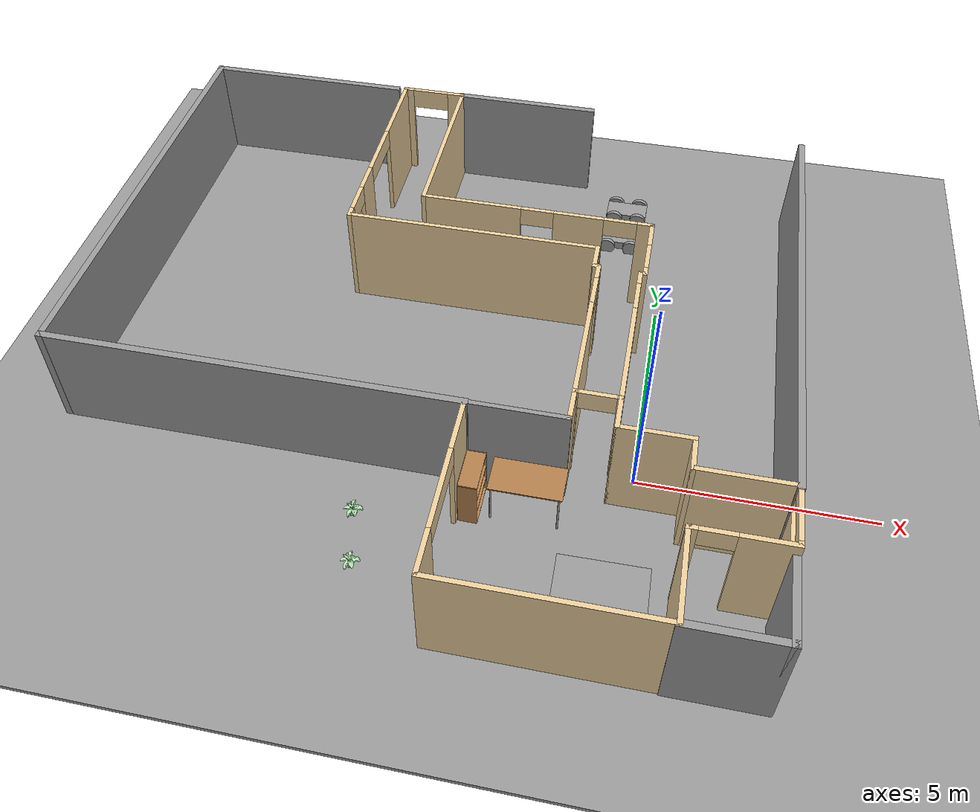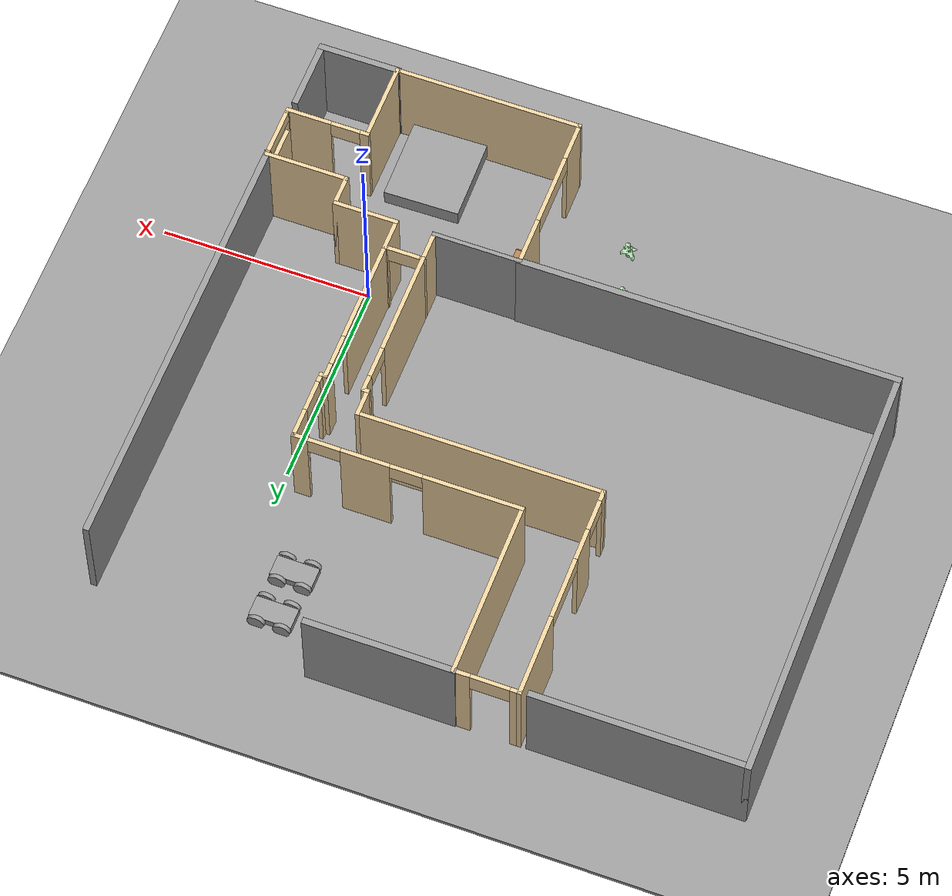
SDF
<sdf version="1.6">
 <world name="default">
  <plugin name="hello" filename="libhello_project1.so"/>
  <light name="sun" type="directional">
   <pose>0 0 10 0 -0 0</pose>
   <diffuse>0.8 0.8 0.8 1</diffuse>
   <specular>0.2 0.2 0.2 1</specular>
   <attenuation>
    <range>1000</range>
    <constant>0.9</constant>
    <linear>0.01</linear>
    <quadratic>0.001</quadratic>
   </attenuation>
   <direction>-0.5 0.1 -0.9</direction>
  </light>
  <model name="ground_plane">
   <static>1</static>
   <link name="link">
    <collision name="collision">
     <geometry><plane><normal>0 0 1</normal><size>100 100</size></plane></geometry>
     <surface><friction><ode><mu>100</mu><mu2>50</mu2></ode></friction></surface>
    </collision>
    <visual name="visual">
     <cast_shadows>0</cast_shadows>
     <geometry><plane><normal>0 0 1</normal><size>100 100</size></plane></geometry>
     <material>
      <script><uri>file://media/materials/scripts/gazebo.material</uri><name>Gazebo/Grey</name></script>
     </material>
    </visual>
   </link>
  </model>
  <gravity>0 0 -9.8</gravity>
  <magnetic_field>6e-06 2.3e-05 -4.2e-05</magnetic_field>
  <atmosphere type="adiabatic"/>
  <physics name="default_physics" default="0" type="ode">
   <max_step_size>0.001</max_step_size>
   <real_time_factor>1</real_time_factor>
   <real_time_update_rate>1000</real_time_update_rate>
  </physics>
  <scene><ambient>0.4 0.4 0.4 1</ambient><background>0.7 0.7 0.7 1</background><shadows>1</shadows></scene>
  <spherical_coordinates>
   <surface_model>EARTH_WGS84</surface_model>
   <latitude_deg>0</latitude_deg>
   <longitude_deg>0</longitude_deg>
   <elevation>0</elevation>
   <heading_deg>0</heading_deg>
  </spherical_coordinates>
  <model name="myroom">
   <pose>-4.68363 2.51363 0 0 -0 0</pose>
   <link name="Wall_19">
    <collision name="Wall_19_Collision">
     <geometry><box><size>0.81 0.1 2.5</size></box></geometry>
     <pose>0 0 1.25 0 -0 0</pose>
    </collision>
    <visual name="Wall_19_Visual">
     <pose>0 0 1.25 0 -0 0</pose>
     <geometry><box><size>0.81 0.1 2.5</size></box></geometry>
     <material>
      <script><uri>file://media/materials/scripts/gazebo.material</uri><name>Gazebo/Grey</name></script>
      <ambient>0.921569 0.807843 0.615686 1</ambient>
     </material>
     <meta><layer>0</layer></meta>
    </visual>
    <pose>4.2 -2.785 0 0 0 -1.5708</pose>
   </link>
   <link name="Wall_22">
    <collision name="Wall_22_Collision">
     <geometry><box><size>1.57 0.1 2.5</size></box></geometry>
     <pose>0 0 1.25 0 -0 0</pose>
    </collision>
    <visual name="Wall_22_Visual">
     <pose>0 0 1.25 0 -0 0</pose>
     <geometry><box><size>1.57 0.1 2.5</size></box></geometry>
     <material>
      <script><uri>file://media/materials/scripts/gazebo.material</uri><name>Gazebo/Grey</name></script>
      <ambient>0.921569 0.807843 0.615686 1</ambient>
     </material>
     <meta><layer>0</layer></meta>
    </visual>
    <pose>4.935 -3.14 0 0 -0 0</pose>
   </link>
   <link name="Wall_24">
    <collision name="Wall_24_Collision">
     <geometry><box><size>0.79 0.1 2.5</size></box></geometry>
     <pose>0 0 1.25 0 -0 0</pose>
    </collision>
    <visual name="Wall_24_Visual">
     <pose>0 0 1.25 0 -0 0</pose>
     <geometry><box><size>0.79 0.1 2.5</size></box></geometry>
     <material>
      <script><uri>file://media/materials/scripts/gazebo.material</uri><name>Gazebo/Grey</name></script>
      <ambient>0.921569 0.807843 0.615686 1</ambient>
     </material>
     <meta><layer>0</layer></meta>
    </visual>
    <pose>5.67 -3.485 0 0 0 -1.5708</pose>
   </link>
   <link name="Wall_26">
    <collision name="Wall_26_Collision">
     <geometry><box><size>2.03 0.1 2.5</size></box></geometry>
     <pose>0 0 1.25 0 -0 0</pose>
    </collision>
    <visual name="Wall_26_Visual">
     <pose>0 0 1.25 0 -0 0</pose>
     <geometry><box><size>2.03 0.1 2.5</size></box></geometry>
     <material>
      <script><uri>file://media/materials/scripts/gazebo.material</uri><name>Gazebo/Grey</name></script>
      <ambient>0.921569 0.807843 0.615686 1</ambient>
     </material>
     <meta><layer>0</layer></meta>
    </visual>
    <pose>6.635 -3.83 0 0 -0 0</pose>
   </link>
   <link name="Wall_28">
    <pose>7.6 -4.475 0 0 0 -1.5708</pose>
    <visual name="Wall_28_Visual_0">
     <pose>-0.621782 0 1.25 0 -0 0</pose>
     <geometry><box><size>0.146436 0.1 2.5</size></box></geometry>
     <material>
      <script><uri>file://media/materials/scripts/gazebo.material</uri><name>Gazebo/Grey</name></script>
      <ambient>0.921569 0.807843 0.615686 1</ambient>
     </material>
     <meta><layer>0</layer></meta>
    </visual>
    <collision name="Wall_28_Collision_0">
     <geometry><box><size>0.146436 0.1 2.5</size></box></geometry>
     <pose>-0.621782 0 1.25 0 -0 0</pose>
    </collision>
    <visual name="Wall_28_Visual_1">
     <pose>0.073218 0 0.9 0 -0 0</pose>
     <geometry><box><size>1.24356 0.1 1.8</size></box></geometry>
     <material>
      <script><uri>file://media/materials/scripts/gazebo.material</uri><name>Gazebo/Grey</name></script>
      <ambient>0.921569 0.807843 0.615686 1</ambient>
     </material>
     <meta><layer>0</layer></meta>
    </visual>
    <collision name="Wall_28_Collision_1">
     <geometry><box><size>1.24356 0.1 1.8</size></box></geometry>
     <pose>0.073218 0 0.9 0 -0 0</pose>
    </collision>
    <visual name="Wall_28_Visual_2">
     <pose>0.623218 0 2.15 0 -0 0</pose>
     <geometry><box><size>0.143564 0.1 0.7</size></box></geometry>
     <material>
      <script><uri>file://media/materials/scripts/gazebo.material</uri><name>Gazebo/Grey</name></script>
      <ambient>0.921569 0.807843 0.615686 1</ambient>
     </material>
     <meta><layer>0</layer></meta>
    </visual>
    <collision name="Wall_28_Collision_2">
     <geometry><box><size>0.143564 0.1 0.7</size></box></geometry>
     <pose>0.623218 0 2.15 0 -0 0</pose>
    </collision>
    <visual name="Wall_28_Visual_3">
     <pose>0.001436 0 2.35 0 -0 0</pose>
     <geometry><box><size>1.1 0.1 0.3</size></box></geometry>
     <material>
      <script><uri>file://media/materials/scripts/gazebo.material</uri><name>Gazebo/Grey</name></script>
      <ambient>0.921569 0.807843 0.615686 1</ambient>
     </material>
     <meta><layer>0</layer></meta>
    </visual>
    <collision name="Wall_28_Collision_3">
     <geometry><box><size>1.1 0.1 0.3</size></box></geometry>
     <pose>0.001436 0 2.35 0 -0 0</pose>
    </collision>
   </link>
   <link name="Wall_30">
    <pose>6.635 -5.12 0 0 -0 3.14159</pose>
    <visual name="Wall_30_Visual_0">
     <pose>-0.459913 0 1.25 0 -0 0</pose>
     <geometry><box><size>1.11017 0.1 2.5</size></box></geometry>
     <material>
      <script><uri>file://media/materials/scripts/gazebo.material</uri><name>Gazebo/Grey</name></script>
      <ambient>0.921569 0.807843 0.615686 1</ambient>
     </material>
     <meta><layer>0</layer></meta>
    </visual>
    <collision name="Wall_30_Collision_0">
     <geometry><box><size>1.11017 0.1 2.5</size></box></geometry>
     <pose>-0.459913 0 1.25 0 -0 0</pose>
    </collision>
    <visual name="Wall_30_Visual_1">
     <pose>0.905087 0 1.25 0 -0 0</pose>
     <geometry><box><size>0.219825 0.1 2.5</size></box></geometry>
     <material>
      <script><uri>file://media/materials/scripts/gazebo.material</uri><name>Gazebo/Grey</name></script>
      <ambient>0.921569 0.807843 0.615686 1</ambient>
     </material>
     <meta><layer>0</layer></meta>
    </visual>
    <collision name="Wall_30_Collision_1">
     <geometry><box><size>0.219825 0.1 2.5</size></box></geometry>
     <pose>0.905087 0 1.25 0 -0 0</pose>
    </collision>
    <visual name="Wall_30_Visual_2">
     <pose>0.445175 0 2.275 0 -0 0</pose>
     <geometry><box><size>0.7 0.1 0.45</size></box></geometry>
     <material>
      <script><uri>file://media/materials/scripts/gazebo.material</uri><name>Gazebo/Grey</name></script>
      <ambient>0.921569 0.807843 0.615686 1</ambient>
     </material>
     <meta><layer>0</layer></meta>
    </visual>
    <collision name="Wall_30_Collision_2">
     <geometry><box><size>0.7 0.1 0.45</size></box></geometry>
     <pose>0.445175 0 2.275 0 -0 0</pose>
    </collision>
   </link>
   <link name="Wall_32">
    <collision name="Wall_32_Collision">
     <geometry><box><size>1.99 0.1 2.5</size></box></geometry>
     <pose>0 0 1.25 0 -0 0</pose>
    </collision>
    <visual name="Wall_32_Visual">
     <pose>0 0 1.25 0 -0 0</pose>
     <geometry><box><size>1.99 0.1 2.5</size></box></geometry>
     <material>
      <script><uri>file://media/materials/scripts/gazebo.material</uri><name>Gazebo/Grey</name></script>
      <ambient>0.921569 0.807843 0.615686 1</ambient>
     </material>
     <meta><layer>0</layer></meta>
    </visual>
    <pose>5.67 -6.065 0 0 0 -1.5708</pose>
   </link>
   <link name="Wall_34">
    <collision name="Wall_34_Collision">
     <geometry><box><size>4.52 0.1 2.5</size></box></geometry>
     <pose>0 0 1.25 0 -0 0</pose>
    </collision>
    <visual name="Wall_34_Visual">
     <pose>0 0 1.25 0 -0 0</pose>
     <geometry><box><size>4.52 0.1 2.5</size></box></geometry>
     <material>
      <script><uri>file://media/materials/scripts/gazebo.material</uri><name>Gazebo/Grey</name></script>
      <ambient>0.921569 0.807843 0.615686 1</ambient>
     </material>
     <meta><layer>0</layer></meta>
    </visual>
    <pose>3.46 -7.01 0 0 -0 3.14159</pose>
   </link>
   <link name="Wall_36">
    <pose>1.25 -5.0735 0 0 -0 1.5708</pose>
    <visual name="Wall_36_Visual_0">
     <pose>-1.4907 0 1.25 0 -0 0</pose>
     <geometry><box><size>0.991176 0.1 2.5</size></box></geometry>
     <material>
      <script><uri>file://media/materials/scripts/gazebo.material</uri><name>Gazebo/Grey</name></script>
      <ambient>0.921569 0.807843 0.615686 1</ambient>
     </material>
     <meta><layer>0</layer></meta>
    </visual>
    <collision name="Wall_36_Collision_0">
     <geometry><box><size>0.991176 0.1 2.5</size></box></geometry>
     <pose>-1.4907 0 1.25 0 -0 0</pose>
    </collision>
    <visual name="Wall_36_Visual_1">
     <pose>0.495588 0 0.005 0 -0 0</pose>
     <geometry><box><size>2.9814 0.1 0.01</size></box></geometry>
     <material>
      <script><uri>file://media/materials/scripts/gazebo.material</uri><name>Gazebo/Grey</name></script>
      <ambient>0.921569 0.807843 0.615686 1</ambient>
     </material>
     <meta><layer>0</layer></meta>
    </visual>
    <collision name="Wall_36_Collision_1">
     <geometry><box><size>2.9814 0.1 0.01</size></box></geometry>
     <pose>0.495588 0 0.005 0 -0 0</pose>
    </collision>
    <visual name="Wall_36_Visual_2">
     <pose>1.38559 0 1.255 0 -0 0</pose>
     <geometry><box><size>1.2014 0.1 2.49</size></box></geometry>
     <material>
      <script><uri>file://media/materials/scripts/gazebo.material</uri><name>Gazebo/Grey</name></script>
      <ambient>0.921569 0.807843 0.615686 1</ambient>
     </material>
     <meta><layer>0</layer></meta>
    </visual>
    <collision name="Wall_36_Collision_2">
     <geometry><box><size>1.2014 0.1 2.49</size></box></geometry>
     <pose>1.38559 0 1.255 0 -0 0</pose>
    </collision>
    <visual name="Wall_36_Visual_3">
     <pose>-0.105111 0 2.255 0 -0 0</pose>
     <geometry><box><size>1.78 0.1 0.49</size></box></geometry>
     <material>
      <script><uri>file://media/materials/scripts/gazebo.material</uri><name>Gazebo/Grey</name></script>
      <ambient>0.921569 0.807843 0.615686 1</ambient>
     </material>
     <meta><layer>0</layer></meta>
    </visual>
    <collision name="Wall_36_Collision_3">
     <geometry><box><size>1.78 0.1 0.49</size></box></geometry>
     <pose>-0.105111 0 2.255 0 -0 0</pose>
    </collision>
   </link>
   <link name="Wall_38">
    <pose>3.745 -2.43 0 0 -0 3.14159</pose>
    <visual name="Wall_38_Visual_0">
     <pose>-0.442506 0 1.25 0 -0 0</pose>
     <geometry><box><size>0.124989 0.1 2.5</size></box></geometry>
     <material>
      <script><uri>file://media/materials/scripts/gazebo.material</uri><name>Gazebo/Grey</name></script>
      <ambient>0.921569 0.807843 0.615686 1</ambient>
     </material>
     <meta><layer>0</layer></meta>
    </visual>
    <collision name="Wall_38_Collision_0">
     <geometry><box><size>0.124989 0.1 2.5</size></box></geometry>
     <pose>-0.442506 0 1.25 0 -0 0</pose>
    </collision>
    <visual name="Wall_38_Visual_1">
     <pose>0.442494 0 1.25 0 -0 0</pose>
     <geometry><box><size>0.125011 0.1 2.5</size></box></geometry>
     <material>
      <script><uri>file://media/materials/scripts/gazebo.material</uri><name>Gazebo/Grey</name></script>
      <ambient>0.921569 0.807843 0.615686 1</ambient>
     </material>
     <meta><layer>0</layer></meta>
    </visual>
    <collision name="Wall_38_Collision_1">
     <geometry><box><size>0.125011 0.1 2.5</size></box></geometry>
     <pose>0.442494 0 1.25 0 -0 0</pose>
    </collision>
    <visual name="Wall_38_Visual_2">
     <pose>-1.1e-05 0 2.275 0 -0 0</pose>
     <geometry><box><size>0.76 0.1 0.45</size></box></geometry>
     <material>
      <script><uri>file://media/materials/scripts/gazebo.material</uri><name>Gazebo/Grey</name></script>
      <ambient>0.921569 0.807843 0.615686 1</ambient>
     </material>
     <meta><layer>0</layer></meta>
    </visual>
    <collision name="Wall_38_Collision_2">
     <geometry><box><size>0.76 0.1 0.45</size></box></geometry>
     <pose>-1.1e-05 0 2.275 0 -0 0</pose>
    </collision>
   </link>
   <link name="Wall_43">
    <collision name="Wall_43_Collision">
     <geometry><box><size>0.8 0.1 2.5</size></box></geometry>
     <pose>0 0 1.25 0 -0 0</pose>
    </collision>
    <visual name="Wall_43_Visual">
     <pose>0 0 1.25 0 -0 0</pose>
     <geometry><box><size>0.8 0.1 2.5</size></box></geometry>
     <material>
      <script><uri>file://media/materials/scripts/gazebo.material</uri><name>Gazebo/Grey</name></script>
      <ambient>0.921569 0.807843 0.615686 1</ambient>
     </material>
     <meta><layer>0</layer></meta>
    </visual>
    <pose>3.29 -2.78 0 0 0 -1.5708</pose>
   </link>
   <link name="Wall_48">
    <collision name="Wall_48_Collision">
     <geometry><box><size>2.14 0.1 2.5</size></box></geometry>
     <pose>0 0 1.25 0 -0 0</pose>
    </collision>
    <visual name="Wall_48_Visual">
     <pose>0 0 1.25 0 -0 0</pose>
     <geometry><box><size>2.14 0.1 2.5</size></box></geometry>
     <material>
      <script><uri>file://media/materials/scripts/gazebo.material</uri><name>Gazebo/Grey</name></script>
      <ambient>1 1 1 1</ambient>
     </material>
     <meta><layer>0</layer></meta>
    </visual>
    <pose>2.27 -3.13 0 0 -0 3.14159</pose>
   </link>
   <link name="Wall_50">
    <pose>3.29 -0.61 0 0 -0 1.5708</pose>
    <visual name="Wall_50_Visual_0">
     <pose>-0.593478 0 1.25 0 -0 0</pose>
     <geometry><box><size>2.55304 0.1 2.5</size></box></geometry>
     <material>
      <script><uri>file://media/materials/scripts/gazebo.material</uri><name>Gazebo/Grey</name></script>
      <ambient>0.921569 0.807843 0.615686 1</ambient>
     </material>
     <meta><layer>0</layer></meta>
    </visual>
    <collision name="Wall_50_Collision_0">
     <geometry><box><size>2.55304 0.1 2.5</size></box></geometry>
     <pose>-0.593478 0 1.25 0 -0 0</pose>
    </collision>
    <visual name="Wall_50_Visual_1">
     <pose>1.65652 0 1.25 0 -0 0</pose>
     <geometry><box><size>0.426956 0.1 2.5</size></box></geometry>
     <material>
      <script><uri>file://media/materials/scripts/gazebo.material</uri><name>Gazebo/Grey</name></script>
      <ambient>0.921569 0.807843 0.615686 1</ambient>
     </material>
     <meta><layer>0</layer></meta>
    </visual>
    <collision name="Wall_50_Collision_1">
     <geometry><box><size>0.426956 0.1 2.5</size></box></geometry>
     <pose>1.65652 0 1.25 0 -0 0</pose>
    </collision>
    <visual name="Wall_50_Visual_2">
     <pose>1.06304 0 2.275 0 -0 0</pose>
     <geometry><box><size>0.76 0.1 0.45</size></box></geometry>
     <material>
      <script><uri>file://media/materials/scripts/gazebo.material</uri><name>Gazebo/Grey</name></script>
      <ambient>0.921569 0.807843 0.615686 1</ambient>
     </material>
     <meta><layer>0</layer></meta>
    </visual>
    <collision name="Wall_50_Collision_2">
     <geometry><box><size>0.76 0.1 0.45</size></box></geometry>
     <pose>1.06304 0 2.275 0 -0 0</pose>
    </collision>
   </link>
   <link name="Wall_52">
    <collision name="Wall_52_Collision">
     <geometry><box><size>0.2 0.1 2.5</size></box></geometry>
     <pose>0 0 1.25 0 -0 0</pose>
    </collision>
    <visual name="Wall_52_Visual">
     <pose>0 0 1.25 0 -0 0</pose>
     <geometry><box><size>0.2 0.1 2.5</size></box></geometry>
     <material>
      <script><uri>file://media/materials/scripts/gazebo.material</uri><name>Gazebo/Grey</name></script>
      <ambient>0.921569 0.807843 0.615686 1</ambient>
     </material>
     <meta><layer>0</layer></meta>
    </visual>
    <pose>3.24 1.21 0 0 -0 3.14159</pose>
   </link>
   <link name="Wall_53">
    <collision name="Wall_53_Collision">
     <geometry><box><size>0.7 0.1 2.5</size></box></geometry>
     <pose>0 0 1.25 0 -0 0</pose>
    </collision>
    <visual name="Wall_53_Visual">
     <pose>0 0 1.25 0 -0 0</pose>
     <geometry><box><size>0.7 0.1 2.5</size></box></geometry>
     <material>
      <script><uri>file://media/materials/scripts/gazebo.material</uri><name>Gazebo/Grey</name></script>
      <ambient>0.921569 0.807843 0.615686 1</ambient>
     </material>
     <meta><layer>0</layer></meta>
    </visual>
    <pose>3.19 1.51 0 0 -0 1.5708</pose>
   </link>
   <link name="Wall_54">
    <collision name="Wall_54_Collision">
     <geometry><box><size>5.8 0.1 2.5</size></box></geometry>
     <pose>0 0 1.25 0 -0 0</pose>
    </collision>
    <visual name="Wall_54_Visual">
     <pose>0 0 1.25 0 -0 0</pose>
     <geometry><box><size>5.8 0.1 2.5</size></box></geometry>
     <material>
      <script><uri>file://media/materials/scripts/gazebo.material</uri><name>Gazebo/Grey</name></script>
      <ambient>0.921569 0.807843 0.615686 1</ambient>
     </material>
     <meta><layer>0</layer></meta>
    </visual>
    <pose>0.34 1.81 0 0 -0 3.14159</pose>
   </link>
   <link name="Wall_56">
    <pose>4.2 -0.63 0 0 -0 1.5708</pose>
    <visual name="Wall_56_Visual_0">
     <pose>-0.569733 0 1.25 0 -0 0</pose>
     <geometry><box><size>2.56053 0.1 2.5</size></box></geometry>
     <material>
      <script><uri>file://media/materials/scripts/gazebo.material</uri><name>Gazebo/Grey</name></script>
      <ambient>0.921569 0.807843 0.615686 1</ambient>
     </material>
     <meta><layer>0</layer></meta>
    </visual>
    <collision name="Wall_56_Collision_0">
     <geometry><box><size>2.56053 0.1 2.5</size></box></geometry>
     <pose>-0.569733 0 1.25 0 -0 0</pose>
    </collision>
    <visual name="Wall_56_Visual_1">
     <pose>1.66027 0 1.25 0 -0 0</pose>
     <geometry><box><size>0.379466 0.1 2.5</size></box></geometry>
     <material>
      <script><uri>file://media/materials/scripts/gazebo.material</uri><name>Gazebo/Grey</name></script>
      <ambient>0.921569 0.807843 0.615686 1</ambient>
     </material>
     <meta><layer>0</layer></meta>
    </visual>
    <collision name="Wall_56_Collision_1">
     <geometry><box><size>0.379466 0.1 2.5</size></box></geometry>
     <pose>1.66027 0 1.25 0 -0 0</pose>
    </collision>
    <visual name="Wall_56_Visual_2">
     <pose>1.09053 0 2.275 0 -0 0</pose>
     <geometry><box><size>0.76 0.1 0.45</size></box></geometry>
     <material>
      <script><uri>file://media/materials/scripts/gazebo.material</uri><name>Gazebo/Grey</name></script>
      <ambient>0.921569 0.807843 0.615686 1</ambient>
     </material>
     <meta><layer>0</layer></meta>
    </visual>
    <collision name="Wall_56_Collision_2">
     <geometry><box><size>0.76 0.1 0.45</size></box></geometry>
     <pose>1.09053 0 2.275 0 -0 0</pose>
    </collision>
   </link>
   <link name="Wall_57">
    <collision name="Wall_57_Collision">
     <geometry><box><size>0.2 0.1 2.5</size></box></geometry>
     <pose>0 0 1.25 0 -0 0</pose>
    </collision>
    <visual name="Wall_57_Visual">
     <pose>0 0 1.25 0 -0 0</pose>
     <geometry><box><size>0.2 0.1 2.5</size></box></geometry>
     <material>
      <script><uri>file://media/materials/scripts/gazebo.material</uri><name>Gazebo/Grey</name></script>
      <ambient>0.921569 0.807843 0.615686 1</ambient>
     </material>
     <meta><layer>0</layer></meta>
    </visual>
    <pose>4.25 1.17 0 0 -0 0</pose>
   </link>
   <link name="Wall_58">
    <pose>4.3 1.97 0 0 -0 1.5708</pose>
    <visual name="Wall_58_Visual_0">
     <pose>-0.725824 0 1.25 0 -0 0</pose>
     <geometry><box><size>0.248351 0.1 2.5</size></box></geometry>
     <material>
      <script><uri>file://media/materials/scripts/gazebo.material</uri><name>Gazebo/Grey</name></script>
      <ambient>0.921569 0.807843 0.615686 1</ambient>
     </material>
     <meta><layer>0</layer></meta>
    </visual>
    <collision name="Wall_58_Collision_0">
     <geometry><box><size>0.248351 0.1 2.5</size></box></geometry>
     <pose>-0.725824 0 1.25 0 -0 0</pose>
    </collision>
    <visual name="Wall_58_Visual_1">
     <pose>0.504176 0 1.25 0 -0 0</pose>
     <geometry><box><size>0.691649 0.1 2.5</size></box></geometry>
     <material>
      <script><uri>file://media/materials/scripts/gazebo.material</uri><name>Gazebo/Grey</name></script>
      <ambient>0.921569 0.807843 0.615686 1</ambient>
     </material>
     <meta><layer>0</layer></meta>
    </visual>
    <collision name="Wall_58_Collision_1">
     <geometry><box><size>0.691649 0.1 2.5</size></box></geometry>
     <pose>0.504176 0 1.25 0 -0 0</pose>
    </collision>
    <visual name="Wall_58_Visual_2">
     <pose>-0.221649 0 2.275 0 -0 0</pose>
     <geometry><box><size>0.76 0.1 0.45</size></box></geometry>
     <material>
      <script><uri>file://media/materials/scripts/gazebo.material</uri><name>Gazebo/Grey</name></script>
      <ambient>0.921569 0.807843 0.615686 1</ambient>
     </material>
     <meta><layer>0</layer></meta>
    </visual>
    <collision name="Wall_58_Collision_2">
     <geometry><box><size>0.76 0.1 0.45</size></box></geometry>
     <pose>-0.221649 0 2.275 0 -0 0</pose>
    </collision>
   </link>
   <link name="Wall_62">
    <pose>-2.51 4.41 0 0 -0 1.5708</pose>
    <visual name="Wall_62_Visual_0">
     <pose>-2.51076 0 1.25 0 -0 0</pose>
     <geometry><box><size>0.278473 0.1 2.5</size></box></geometry>
     <material>
      <script><uri>file://media/materials/scripts/gazebo.material</uri><name>Gazebo/Grey</name></script>
      <ambient>0.921569 0.807843 0.615686 1</ambient>
     </material>
     <meta><layer>0</layer></meta>
    </visual>
    <collision name="Wall_62_Collision_0">
     <geometry><box><size>0.278473 0.1 2.5</size></box></geometry>
     <pose>-2.51076 0 1.25 0 -0 0</pose>
    </collision>
    <visual name="Wall_62_Visual_1">
     <pose>-1.2242 0 1.25 0 -0 0</pose>
     <geometry><box><size>0.774661 0.1 2.5</size></box></geometry>
     <material>
      <script><uri>file://media/materials/scripts/gazebo.material</uri><name>Gazebo/Grey</name></script>
      <ambient>0.921569 0.807843 0.615686 1</ambient>
     </material>
     <meta><layer>0</layer></meta>
    </visual>
    <collision name="Wall_62_Collision_1">
     <geometry><box><size>0.774661 0.1 2.5</size></box></geometry>
     <pose>-1.2242 0 1.25 0 -0 0</pose>
    </collision>
    <visual name="Wall_62_Visual_2">
     <pose>1.65657 0 1.25 0 -0 0</pose>
     <geometry><box><size>1.98687 0.1 2.5</size></box></geometry>
     <material>
      <script><uri>file://media/materials/scripts/gazebo.material</uri><name>Gazebo/Grey</name></script>
      <ambient>0.921569 0.807843 0.615686 1</ambient>
     </material>
     <meta><layer>0</layer></meta>
    </visual>
    <collision name="Wall_62_Collision_2">
     <geometry><box><size>1.98687 0.1 2.5</size></box></geometry>
     <pose>1.65657 0 1.25 0 -0 0</pose>
    </collision>
    <visual name="Wall_62_Visual_3">
     <pose>-1.99153 0 2.275 0 -0 0</pose>
     <geometry><box><size>0.76 0.1 0.45</size></box></geometry>
     <material>
      <script><uri>file://media/materials/scripts/gazebo.material</uri><name>Gazebo/Grey</name></script>
      <ambient>0.921569 0.807843 0.615686 1</ambient>
     </material>
     <meta><layer>0</layer></meta>
    </visual>
    <collision name="Wall_62_Collision_3">
     <geometry><box><size>0.76 0.1 0.45</size></box></geometry>
     <pose>-1.99153 0 2.275 0 -0 0</pose>
    </collision>
    <visual name="Wall_62_Visual_4">
     <pose>-0.086866 0 2.275 0 -0 0</pose>
     <geometry><box><size>1.5 0.1 0.45</size></box></geometry>
     <material>
      <script><uri>file://media/materials/scripts/gazebo.material</uri><name>Gazebo/Grey</name></script>
      <ambient>0.921569 0.807843 0.615686 1</ambient>
     </material>
     <meta><layer>0</layer></meta>
    </visual>
    <collision name="Wall_62_Collision_4">
     <geometry><box><size>1.5 0.1 0.45</size></box></geometry>
     <pose>-0.086866 0 2.275 0 -0 0</pose>
    </collision>
   </link>
   <link name="Wall_64">
    <pose>-1.76 7.01 0 0 -0 0</pose>
    <visual name="Wall_64_Visual_0">
     <pose>-0.668872 0 1.25 0 -0 0</pose>
     <geometry><box><size>0.262256 0.1 2.5</size></box></geometry>
     <material>
      <script><uri>file://media/materials/scripts/gazebo.material</uri><name>Gazebo/Grey</name></script>
      <ambient>0.921569 0.807843 0.615686 1</ambient>
     </material>
     <meta><layer>0</layer></meta>
    </visual>
    <collision name="Wall_64_Collision_0">
     <geometry><box><size>0.262256 0.1 2.5</size></box></geometry>
     <pose>-0.668872 0 1.25 0 -0 0</pose>
    </collision>
    <visual name="Wall_64_Visual_1">
     <pose>0.581128 0 1.25 0 -0 0</pose>
     <geometry><box><size>0.437744 0.1 2.5</size></box></geometry>
     <material>
      <script><uri>file://media/materials/scripts/gazebo.material</uri><name>Gazebo/Grey</name></script>
      <ambient>0.921569 0.807843 0.615686 1</ambient>
     </material>
     <meta><layer>0</layer></meta>
    </visual>
    <collision name="Wall_64_Collision_1">
     <geometry><box><size>0.437744 0.1 2.5</size></box></geometry>
     <pose>0.581128 0 1.25 0 -0 0</pose>
    </collision>
    <visual name="Wall_64_Visual_2">
     <pose>-0.087744 0 2.25 0 -0 0</pose>
     <geometry><box><size>0.9 0.1 0.5</size></box></geometry>
     <material>
      <script><uri>file://media/materials/scripts/gazebo.material</uri><name>Gazebo/Grey</name></script>
      <ambient>0.921569 0.807843 0.615686 1</ambient>
     </material>
     <meta><layer>0</layer></meta>
    </visual>
    <collision name="Wall_64_Collision_2">
     <geometry><box><size>0.9 0.1 0.5</size></box></geometry>
     <pose>-0.087744 0 2.25 0 -0 0</pose>
    </collision>
   </link>
   <link name="Wall_66">
    <collision name="Wall_66_Collision">
     <geometry><box><size>4.30002 0.1 2.5</size></box></geometry>
     <pose>0 0 1.25 0 -0 0</pose>
    </collision>
    <visual name="Wall_66_Visual">
     <pose>0 0 1.25 0 -0 0</pose>
     <geometry><box><size>4.30002 0.1 2.5</size></box></geometry>
     <material>
      <script><uri>file://media/materials/scripts/gazebo.material</uri><name>Gazebo/Grey</name></script>
      <ambient>0.921569 0.807843 0.615686 1</ambient>
     </material>
     <meta><layer>0</layer></meta>
    </visual>
    <pose>-1.01 4.91 0 0 0 -1.5708</pose>
   </link>
   <link name="Wall_68">
    <pose>1.645 2.81 0 0 -0 0</pose>
    <visual name="Wall_68_Visual_0">
     <pose>-1.53066 0 1.25 0 -0 0</pose>
     <geometry><box><size>2.34868 0.1 2.5</size></box></geometry>
     <material>
      <script><uri>file://media/materials/scripts/gazebo.material</uri><name>Gazebo/Grey</name></script>
      <ambient>0.921569 0.807843 0.615686 1</ambient>
     </material>
     <meta><layer>0</layer></meta>
    </visual>
    <collision name="Wall_68_Collision_0">
     <geometry><box><size>2.34868 0.1 2.5</size></box></geometry>
     <pose>-1.53066 0 1.25 0 -0 0</pose>
    </collision>
    <visual name="Wall_68_Visual_1">
     <pose>0.980366 0 1.25 0 -0 0</pose>
     <geometry><box><size>1.15337 0.1 2.5</size></box></geometry>
     <material>
      <script><uri>file://media/materials/scripts/gazebo.material</uri><name>Gazebo/Grey</name></script>
      <ambient>0.921569 0.807843 0.615686 1</ambient>
     </material>
     <meta><layer>0</layer></meta>
    </visual>
    <collision name="Wall_68_Collision_1">
     <geometry><box><size>1.15337 0.1 2.5</size></box></geometry>
     <pose>0.980366 0 1.25 0 -0 0</pose>
    </collision>
    <visual name="Wall_68_Visual_2">
     <pose>2.51103 0 1.25 0 -0 0</pose>
     <geometry><box><size>0.387948 0.1 2.5</size></box></geometry>
     <material>
      <script><uri>file://media/materials/scripts/gazebo.material</uri><name>Gazebo/Grey</name></script>
      <ambient>0.921569 0.807843 0.615686 1</ambient>
     </material>
     <meta><layer>0</layer></meta>
    </visual>
    <collision name="Wall_68_Collision_2">
     <geometry><box><size>0.387948 0.1 2.5</size></box></geometry>
     <pose>2.51103 0 1.25 0 -0 0</pose>
    </collision>
    <visual name="Wall_68_Visual_3">
     <pose>0.02368 0 2.275 0 -0 0</pose>
     <geometry><box><size>0.76 0.1 0.45</size></box></geometry>
     <material>
      <script><uri>file://media/materials/scripts/gazebo.material</uri><name>Gazebo/Grey</name></script>
      <ambient>0.921569 0.807843 0.615686 1</ambient>
     </material>
     <meta><layer>0</layer></meta>
    </visual>
    <collision name="Wall_68_Collision_3">
     <geometry><box><size>0.76 0.1 0.45</size></box></geometry>
     <pose>0.02368 0 2.275 0 -0 0</pose>
    </collision>
    <visual name="Wall_68_Visual_4">
     <pose>1.93705 0 2.275 0 -0 0</pose>
     <geometry><box><size>0.76 0.1 0.45</size></box></geometry>
     <material>
      <script><uri>file://media/materials/scripts/gazebo.material</uri><name>Gazebo/Grey</name></script>
      <ambient>0.921569 0.807843 0.615686 1</ambient>
     </material>
     <meta><layer>0</layer></meta>
    </visual>
    <collision name="Wall_68_Collision_4">
     <geometry><box><size>0.76 0.1 0.45</size></box></geometry>
     <pose>1.93705 0 2.275 0 -0 0</pose>
    </collision>
   </link>
   <link name="Wall_70">
    <collision name="Wall_70_Collision">
     <geometry><box><size>9 0.15 2.5</size></box></geometry>
     <pose>0 0 1.25 0 -0 0</pose>
    </collision>
    <visual name="Wall_70_Visual">
     <pose>0 0 1.25 0 -0 0</pose>
     <geometry><box><size>9 0.15 2.5</size></box></geometry>
     <material>
      <script><uri>file://media/materials/scripts/gazebo.material</uri><name>Gazebo/Grey</name></script>
      <ambient>1 1 1 1</ambient>
     </material>
     <meta><layer>0</layer></meta>
    </visual>
    <pose>-3.175 -3.13 0 0 -0 3.14159</pose>
   </link>
   <link name="Wall_71">
    <collision name="Wall_71_Collision">
     <geometry><box><size>10.25 0.15 2.5</size></box></geometry>
     <pose>0 0 1.25 0 -0 0</pose>
    </collision>
    <visual name="Wall_71_Visual">
     <pose>0 0 1.25 0 -0 0</pose>
     <geometry><box><size>10.25 0.15 2.5</size></box></geometry>
     <material>
      <script><uri>file://media/materials/scripts/gazebo.material</uri><name>Gazebo/Grey</name></script>
      <ambient>1 1 1 1</ambient>
     </material>
     <meta><layer>0</layer></meta>
    </visual>
    <pose>-7.6 1.92 0 0 -0 1.5708</pose>
   </link>
   <link name="Wall_72">
    <collision name="Wall_72_Collision">
     <geometry><box><size>5 0.15 2.5</size></box></geometry>
     <pose>0 0 1.25 0 -0 0</pose>
    </collision>
    <visual name="Wall_72_Visual">
     <pose>0 0 1.25 0 -0 0</pose>
     <geometry><box><size>5 0.15 2.5</size></box></geometry>
     <material>
      <script><uri>file://media/materials/scripts/gazebo.material</uri><name>Gazebo/Grey</name></script>
      <ambient>1 1 1 1</ambient>
     </material>
     <meta><layer>0</layer></meta>
    </visual>
    <pose>-5.175 6.97 0 0 -0 0</pose>
   </link>
   <link name="Wall_78">
    <collision name="Wall_78_Collision">
     <geometry><box><size>2 0.15 2.5</size></box></geometry>
     <pose>0 0 1.25 0 -0 0</pose>
    </collision>
    <visual name="Wall_78_Visual">
     <pose>0 0 1.25 0 -0 0</pose>
     <geometry><box><size>2 0.15 2.5</size></box></geometry>
     <material>
      <script><uri>file://media/materials/scripts/gazebo.material</uri><name>Gazebo/Grey</name></script>
      <ambient>1 1 1 1</ambient>
     </material>
     <meta><layer>0</layer></meta>
    </visual>
    <pose>6.595 -7.01 0 0 -0 0</pose>
   </link>
   <link name="Wall_79">
    <collision name="Wall_79_Collision">
     <geometry><box><size>1.75 0.15 2.5</size></box></geometry>
     <pose>0 0 1.25 0 -0 0</pose>
    </collision>
    <visual name="Wall_79_Visual">
     <pose>0 0 1.25 0 -0 0</pose>
     <geometry><box><size>1.75 0.15 2.5</size></box></geometry>
     <material>
      <script><uri>file://media/materials/scripts/gazebo.material</uri><name>Gazebo/Grey</name></script>
      <ambient>1 1 1 1</ambient>
     </material>
     <meta><layer>0</layer></meta>
    </visual>
    <pose>7.52 -6.21 0 0 -0 1.5708</pose>
   </link>
   <link name="Wall_81">
    <collision name="Wall_81_Collision">
     <geometry><box><size>10.5 0.15 2.5</size></box></geometry>
     <pose>0 0 1.25 0 -0 0</pose>
    </collision>
    <visual name="Wall_81_Visual">
     <pose>0 0 1.25 0 -0 0</pose>
     <geometry><box><size>10.5 0.15 2.5</size></box></geometry>
     <material>
      <script><uri>file://media/materials/scripts/gazebo.material</uri><name>Gazebo/Grey</name></script>
      <ambient>1 1 1 1</ambient>
     </material>
     <meta><layer>0</layer></meta>
    </visual>
    <pose>7.6 1.345 0 0 -0 1.5708</pose>
   </link>
   <link name="Wall_83">
    <collision name="Wall_83_Collision">
     <geometry><box><size>3.5 0.15 2.5</size></box></geometry>
     <pose>0 0 1.25 0 -0 0</pose>
    </collision>
    <visual name="Wall_83_Visual">
     <pose>0 0 1.25 0 -0 0</pose>
     <geometry><box><size>3.5 0.15 2.5</size></box></geometry>
     <material>
      <script><uri>file://media/materials/scripts/gazebo.material</uri><name>Gazebo/Grey</name></script>
      <ambient>1 1 1 1</ambient>
     </material>
     <meta><layer>0</layer></meta>
    </visual>
    <pose>0.6765 7.01 0 0 -0 0</pose>
   </link>
   <static>1</static>
  </model>
  <model name="table">
   <static>1</static>
   <link name="link">
    <collision name="surface">
     <pose>0 0 1 0 -0 0</pose>
     <geometry><box><size>1.5 0.8 0.03</size></box></geometry>
     <surface><friction><ode><mu>0.6</mu><mu2>0.6</mu2></ode></friction></surface>
    </collision>
    <visual name="visual1">
     <pose>0 0 1 0 -0 0</pose>
     <geometry><box><size>1.5 0.8 0.03</size></box></geometry>
     <material>
      <script><uri>file://media/materials/scripts/gazebo.material</uri><name>Gazebo/Wood</name></script>
     </material>
    </visual>
    <collision name="front_left_leg">
     <pose>0.68 0.38 0.5 0 -0 0</pose>
     <geometry><cylinder><radius>0.02</radius><length>1</length></cylinder></geometry>
    </collision>
    <visual name="front_left_leg">
     <pose>0.68 0.38 0.5 0 -0 0</pose>
     <geometry><cylinder><radius>0.02</radius><length>1</length></cylinder></geometry>
     <material>
      <script><uri>file://media/materials/scripts/gazebo.material</uri><name>Gazebo/Grey</name></script>
     </material>
    </visual>
    <collision name="front_right_leg">
     <pose>0.68 -0.38 0.5 0 -0 0</pose>
     <geometry><cylinder><radius>0.02</radius><length>1</length></cylinder></geometry>
    </collision>
    <visual name="front_right_leg">
     <pose>0.68 -0.38 0.5 0 -0 0</pose>
     <geometry><cylinder><radius>0.02</radius><length>1</length></cylinder></geometry>
     <material>
      <script><uri>file://media/materials/scripts/gazebo.material</uri><name>Gazebo/Grey</name></script>
     </material>
    </visual>
    <collision name="back_right_leg">
     <pose>-0.68 -0.38 0.5 0 -0 0</pose>
     <geometry><cylinder><radius>0.02</radius><length>1</length></cylinder></geometry>
    </collision>
    <visual name="back_right_leg">
     <pose>-0.68 -0.38 0.5 0 -0 0</pose>
     <geometry><cylinder><radius>0.02</radius><length>1</length></cylinder></geometry>
     <material>
      <script><uri>file://media/materials/scripts/gazebo.material</uri><name>Gazebo/Grey</name></script>
     </material>
    </visual>
    <collision name="back_left_leg">
     <pose>-0.68 0.38 0.5 0 -0 0</pose>
     <geometry><cylinder><radius>0.02</radius><length>1</length></cylinder></geometry>
    </collision>
    <visual name="back_left_leg">
     <pose>-0.68 0.38 0.5 0 -0 0</pose>
     <geometry><cylinder><radius>0.02</radius><length>1</length></cylinder></geometry>
     <material>
      <script><uri>file://media/materials/scripts/gazebo.material</uri><name>Gazebo/Grey</name></script>
     </material>
    </visual>
   </link>
   <pose>-2.06098 -1.09205 0 0 -0 0</pose>
  </model>
  <model name="bookshelf">
   <static>1</static>
   <link name="link">
    <inertial><mass>1</mass></inertial>
    <collision name="back">
     <pose>0 0.005 0.6 0 -0 0</pose>
     <geometry><box><size>0.9 0.01 1.2</size></box></geometry>
    </collision>
    <visual name="visual1">
     <pose>0 0.005 0.6 0 -0 0</pose>
     <geometry><box><size>0.9 0.01 1.2</size></box></geometry>
     <material>
      <script><uri>file://media/materials/scripts/gazebo.material</uri><name>Gazebo/Wood</name></script>
     </material>
    </visual>
    <collision name="left_side">
     <pose>0.45 -0.195 0.6 0 -0 0</pose>
     <geometry><box><size>0.02 0.4 1.2</size></box></geometry>
    </collision>
    <visual name="visual2">
     <pose>0.45 -0.195 0.6 0 -0 0</pose>
     <geometry><box><size>0.02 0.4 1.2</size></box></geometry>
     <material>
      <script><uri>file://media/materials/scripts/gazebo.material</uri><name>Gazebo/Wood</name></script>
     </material>
    </visual>
    <collision name="right_side">
     <pose>-0.45 -0.195 0.6 0 -0 0</pose>
     <geometry><box><size>0.02 0.4 1.2</size></box></geometry>
    </collision>
    <visual name="visual3">
     <pose>-0.45 -0.195 0.6 0 -0 0</pose>
     <geometry><box><size>0.02 0.4 1.2</size></box></geometry>
     <material>
      <script><uri>file://media/materials/scripts/gazebo.material</uri><name>Gazebo/Wood</name></script>
     </material>
    </visual>
    <collision name="bottom">
     <pose>0 -0.195 0.03 0 -0 0</pose>
     <geometry><box><size>0.88 0.4 0.06</size></box></geometry>
    </collision>
    <visual name="visual4">
     <pose>0 -0.195 0.03 0 -0 0</pose>
     <geometry><box><size>0.88 0.4 0.06</size></box></geometry>
     <material>
      <script><uri>file://media/materials/scripts/gazebo.material</uri><name>Gazebo/Wood</name></script>
     </material>
    </visual>
    <collision name="top">
     <pose>0 -0.195 1.19 0 -0 0</pose>
     <geometry><box><size>0.88 0.4 0.02</size></box></geometry>
    </collision>
    <visual name="visual5">
     <pose>0 -0.195 1.19 0 -0 0</pose>
     <geometry><box><size>0.88 0.4 0.02</size></box></geometry>
     <material>
      <script><uri>file://media/materials/scripts/gazebo.material</uri><name>Gazebo/Wood</name></script>
     </material>
    </visual>
    <collision name="low_shelf">
     <pose>0 -0.195 0.43 0 -0 0</pose>
     <geometry><box><size>0.88 0.4 0.02</size></box></geometry>
    </collision>
    <visual name="visual6">
     <pose>0 -0.195 0.43 0 -0 0</pose>
     <geometry><box><size>0.88 0.4 0.02</size></box></geometry>
     <material>
      <script><uri>file://media/materials/scripts/gazebo.material</uri><name>Gazebo/Wood</name></script>
     </material>
    </visual>
    <collision name="high_shelf">
     <pose>0 -0.195 0.8 0 -0 0</pose>
     <geometry><box><size>0.88 0.4 0.02</size></box></geometry>
    </collision>
    <visual name="visual7">
     <pose>0 -0.195 0.8 0 -0 0</pose>
     <geometry><box><size>0.88 0.4 0.02</size></box></geometry>
     <material>
      <script><uri>file://media/materials/scripts/gazebo.material</uri><name>Gazebo/Wood</name></script>
     </material>
    </visual>
   </link>
   <pose>-3.35633 -1.21986 0 0 -0 1.56092</pose>
  </model>
  <light name="user_point_light_0" type="point">
   <pose>-0.435048 -2.08009 1 0 -0 0</pose>
   <diffuse>0.5 0.5 0.5 1</diffuse>
   <specular>0.1 0.1 0.1 1</specular>
   <attenuation>
    <range>20</range>
    <constant>0.5</constant>
    <linear>0.01</linear>
    <quadratic>0.001</quadratic>
   </attenuation>
   <cast_shadows>0</cast_shadows>
   <direction>0 0 -1</direction>
  </light>
  <light name="user_point_light_1" type="point">
   <pose>-0.897454 1.79348 1 0 -0 0</pose>
   <diffuse>0.5 0.5 0.5 1</diffuse>
   <specular>0.1 0.1 0.1 1</specular>
   <attenuation>
    <range>20</range>
    <constant>0.5</constant>
    <linear>0.01</linear>
    <quadratic>0.001</quadratic>
   </attenuation>
   <cast_shadows>0</cast_shadows>
   <direction>0 0 -1</direction>
  </light>
  <light name="user_point_light_2" type="point">
   <pose>-4.0914 4.7917 1 0 -0 0</pose>
   <diffuse>0.5 0.5 0.5 1</diffuse>
   <specular>0.1 0.1 0.1 1</specular>
   <attenuation>
    <range>20</range>
    <constant>0.5</constant>
    <linear>0.01</linear>
    <quadratic>0.001</quadratic>
   </attenuation>
   <cast_shadows>0</cast_shadows>
   <direction>0 0 -1</direction>
  </light>
  <light name="user_point_light_3" type="point">
   <pose>-7.00004 6.8958 1 0 -0 0</pose>
   <diffuse>0.5 0.5 0.5 1</diffuse>
   <specular>0.1 0.1 0.1 1</specular>
   <attenuation>
    <range>20</range>
    <constant>0.5</constant>
    <linear>0.01</linear>
    <quadratic>0.001</quadratic>
   </attenuation>
   <cast_shadows>0</cast_shadows>
   <direction>0 0 -1</direction>
  </light>
  <model name="bed">
   <link name="link_0">
    <pose>-0.020885 0.186214 -0.326795 0 -0 0</pose>
    <inertial>
     <mass>1</mass>
     <inertia>
      <ixx>0.166667</ixx>
      <ixy>0</ixy>
      <ixz>0</ixz>
      <iyy>0.166667</iyy>
      <iyz>0</iyz>
      <izz>0.166667</izz>
     </inertia>
    </inertial>
    <visual name="visual">
     <geometry><box><size>2 1.8 0.4</size></box></geometry>
     <material>
      <lighting>1</lighting>
      <script><uri>file://media/materials/scripts/gazebo.material</uri><name>Gazebo/Grey</name></script>
      <ambient>0.3 0.3 0.3 1</ambient>
      <diffuse>0.7 0.7 0.7 1</diffuse>
      <specular>0.01 0.01 0.01 1</specular>
      <emissive>0 0 0 1</emissive>
      <shader type="vertex"><normal_map>__default__</normal_map></shader>
     </material>
    </visual>
    <collision name="collision">
     <geometry><box><size>2 1.8 0.4</size></box></geometry>
     <surface>
      <friction>
       <ode><mu>1</mu><mu2>1</mu2><fdir1>0 0 0</fdir1><slip1>0</slip1><slip2>0</slip2></ode>
       <torsional>
        <coefficient>1</coefficient>
        <patch_radius>0</patch_radius>
        <surface_radius>0</surface_radius>
        <use_patch_radius>1</use_patch_radius>
        <ode><slip>0</slip></ode>
       </torsional>
      </friction>
      <bounce><restitution_coefficient>0</restitution_coefficient><threshold>1e+06</threshold></bounce>
      <contact>
       <collide_without_contact>0</collide_without_contact>
       <collide_without_contact_bitmask>1</collide_without_contact_bitmask>
       <collide_bitmask>1</collide_bitmask>
       <ode>
        <soft_cfm>0</soft_cfm>
        <soft_erp>0.2</soft_erp>
        <kp>1e+13</kp>
        <kd>1</kd>
        <max_vel>0.01</max_vel>
        <min_depth>0</min_depth>
       </ode>
       <bullet>
        <split_impulse>1</split_impulse>
        <split_impulse_penetration_threshold>-0.01</split_impulse_penetration_threshold>
        <soft_cfm>0</soft_cfm>
        <soft_erp>0.2</soft_erp>
        <kp>1e+13</kp>
        <kd>1</kd>
       </bullet>
      </contact>
     </surface>
    </collision>
   </link>
   <link name="link_1">
    <pose>-0.770885 -0.563786 -0.001795 0 -0 0</pose>
    <inertial>
     <mass>1</mass>
     <inertia><ixx>0.145833</ixx><ixy>0</ixy><ixz>0</ixz><iyy>0.145833</iyy><iyz>0</iyz><izz>0.125</izz></inertia>
    </inertial>
    <visual name="visual">
     <geometry><cylinder><radius>0.04</radius><length>0.25</length></cylinder></geometry>
     <material>
      <lighting>1</lighting>
      <script><uri>file://media/materials/scripts/gazebo.material</uri><name>Gazebo/Grey</name></script>
      <ambient>0.3 0.3 0.3 1</ambient>
      <diffuse>0.7 0.7 0.7 1</diffuse>
      <specular>0.01 0.01 0.01 1</specular>
      <emissive>0 0 0 1</emissive>
      <shader type="vertex"><normal_map>__default__</normal_map></shader>
     </material>
    </visual>
    <collision name="collision">
     <geometry><cylinder><radius>0.04</radius><length>0.25</length></cylinder></geometry>
     <surface>
      <friction>
       <ode><mu>1</mu><mu2>1</mu2><fdir1>0 0 0</fdir1><slip1>0</slip1><slip2>0</slip2></ode>
       <torsional>
        <coefficient>1</coefficient>
        <patch_radius>0</patch_radius>
        <surface_radius>0</surface_radius>
        <use_patch_radius>1</use_patch_radius>
        <ode><slip>0</slip></ode>
       </torsional>
      </friction>
      <bounce><restitution_coefficient>0</restitution_coefficient><threshold>1e+06</threshold></bounce>
      <contact>
       <collide_without_contact>0</collide_without_contact>
       <collide_without_contact_bitmask>1</collide_without_contact_bitmask>
       <collide_bitmask>1</collide_bitmask>
       <ode>
        <soft_cfm>0</soft_cfm>
        <soft_erp>0.2</soft_erp>
        <kp>1e+13</kp>
        <kd>1</kd>
        <max_vel>0.01</max_vel>
        <min_depth>0</min_depth>
       </ode>
       <bullet>
        <split_impulse>1</split_impulse>
        <split_impulse_penetration_threshold>-0.01</split_impulse_penetration_threshold>
        <soft_cfm>0</soft_cfm>
        <soft_erp>0.2</soft_erp>
        <kp>1e+13</kp>
        <kd>1</kd>
       </bullet>
      </contact>
     </surface>
    </collision>
   </link>
   <link name="link_1_clone">
    <pose>-0.770885 0.936214 -0.001795 0 -0 0</pose>
    <inertial>
     <mass>1</mass>
     <inertia><ixx>0.145833</ixx><ixy>0</ixy><ixz>0</ixz><iyy>0.145833</iyy><iyz>0</iyz><izz>0.125</izz></inertia>
    </inertial>
    <visual name="visual">
     <geometry><cylinder><radius>0.04</radius><length>0.25</length></cylinder></geometry>
     <material>
      <lighting>1</lighting>
      <script><uri>file://media/materials/scripts/gazebo.material</uri><name>Gazebo/Grey</name></script>
      <ambient>0.3 0.3 0.3 1</ambient>
      <diffuse>0.7 0.7 0.7 1</diffuse>
      <specular>0.01 0.01 0.01 1</specular>
      <emissive>0 0 0 1</emissive>
      <shader type="vertex"><normal_map>__default__</normal_map></shader>
     </material>
    </visual>
    <collision name="collision">
     <geometry><cylinder><radius>0.04</radius><length>0.25</length></cylinder></geometry>
     <surface>
      <friction>
       <ode><mu>1</mu><mu2>1</mu2><fdir1>0 0 0</fdir1><slip1>0</slip1><slip2>0</slip2></ode>
       <torsional>
        <coefficient>1</coefficient>
        <patch_radius>0</patch_radius>
        <surface_radius>0</surface_radius>
        <use_patch_radius>1</use_patch_radius>
        <ode><slip>0</slip></ode>
       </torsional>
      </friction>
      <bounce><restitution_coefficient>0</restitution_coefficient><threshold>1e+06</threshold></bounce>
      <contact>
       <collide_without_contact>0</collide_without_contact>
       <collide_without_contact_bitmask>1</collide_without_contact_bitmask>
       <collide_bitmask>1</collide_bitmask>
       <ode>
        <soft_cfm>0</soft_cfm>
        <soft_erp>0.2</soft_erp>
        <kp>1e+13</kp>
        <kd>1</kd>
        <max_vel>0.01</max_vel>
        <min_depth>0</min_depth>
       </ode>
       <bullet>
        <split_impulse>1</split_impulse>
        <split_impulse_penetration_threshold>-0.01</split_impulse_penetration_threshold>
        <soft_cfm>0</soft_cfm>
        <soft_erp>0.2</soft_erp>
        <kp>1e+13</kp>
        <kd>1</kd>
       </bullet>
      </contact>
     </surface>
    </collision>
   </link>
   <link name="link_1_clone_0">
    <pose>0.729115 -0.563786 -0.001795 0 -0 0</pose>
    <inertial>
     <mass>1</mass>
     <inertia><ixx>0.145833</ixx><ixy>0</ixy><ixz>0</ixz><iyy>0.145833</iyy><iyz>0</iyz><izz>0.125</izz></inertia>
    </inertial>
    <visual name="visual">
     <geometry><cylinder><radius>0.04</radius><length>0.25</length></cylinder></geometry>
     <material>
      <lighting>1</lighting>
      <script><uri>file://media/materials/scripts/gazebo.material</uri><name>Gazebo/Grey</name></script>
      <ambient>0.3 0.3 0.3 1</ambient>
      <diffuse>0.7 0.7 0.7 1</diffuse>
      <specular>0.01 0.01 0.01 1</specular>
      <emissive>0 0 0 1</emissive>
      <shader type="vertex"><normal_map>__default__</normal_map></shader>
     </material>
    </visual>
    <collision name="collision">
     <geometry><cylinder><radius>0.04</radius><length>0.25</length></cylinder></geometry>
     <surface>
      <friction>
       <ode><mu>1</mu><mu2>1</mu2><fdir1>0 0 0</fdir1><slip1>0</slip1><slip2>0</slip2></ode>
       <torsional>
        <coefficient>1</coefficient>
        <patch_radius>0</patch_radius>
        <surface_radius>0</surface_radius>
        <use_patch_radius>1</use_patch_radius>
        <ode><slip>0</slip></ode>
       </torsional>
      </friction>
      <bounce><restitution_coefficient>0</restitution_coefficient><threshold>1e+06</threshold></bounce>
      <contact>
       <collide_without_contact>0</collide_without_contact>
       <collide_without_contact_bitmask>1</collide_without_contact_bitmask>
       <collide_bitmask>1</collide_bitmask>
       <ode>
        <soft_cfm>0</soft_cfm>
        <soft_erp>0.2</soft_erp>
        <kp>1e+13</kp>
        <kd>1</kd>
        <max_vel>0.01</max_vel>
        <min_depth>0</min_depth>
       </ode>
       <bullet>
        <split_impulse>1</split_impulse>
        <split_impulse_penetration_threshold>-0.01</split_impulse_penetration_threshold>
        <soft_cfm>0</soft_cfm>
        <soft_erp>0.2</soft_erp>
        <kp>1e+13</kp>
        <kd>1</kd>
       </bullet>
      </contact>
     </surface>
    </collision>
   </link>
   <link name="link_1_clone_1">
    <pose>0.729115 0.936214 -0.001795 0 -0 0</pose>
    <inertial>
     <mass>1</mass>
     <inertia><ixx>0.145833</ixx><ixy>0</ixy><ixz>0</ixz><iyy>0.145833</iyy><iyz>0</iyz><izz>0.125</izz></inertia>
    </inertial>
    <visual name="visual">
     <geometry><cylinder><radius>0.04</radius><length>0.25</length></cylinder></geometry>
     <material>
      <lighting>1</lighting>
      <script><uri>file://media/materials/scripts/gazebo.material</uri><name>Gazebo/Grey</name></script>
      <ambient>0.3 0.3 0.3 1</ambient>
      <diffuse>0.7 0.7 0.7 1</diffuse>
      <specular>0.01 0.01 0.01 1</specular>
      <emissive>0 0 0 1</emissive>
      <shader type="vertex"><normal_map>__default__</normal_map></shader>
     </material>
    </visual>
    <collision name="collision">
     <geometry><cylinder><radius>0.04</radius><length>0.25</length></cylinder></geometry>
     <surface>
      <friction>
       <ode><mu>1</mu><mu2>1</mu2><fdir1>0 0 0</fdir1><slip1>0</slip1><slip2>0</slip2></ode>
       <torsional>
        <coefficient>1</coefficient>
        <patch_radius>0</patch_radius>
        <surface_radius>0</surface_radius>
        <use_patch_radius>1</use_patch_radius>
        <ode><slip>0</slip></ode>
       </torsional>
      </friction>
      <bounce><restitution_coefficient>0</restitution_coefficient><threshold>1e+06</threshold></bounce>
      <contact>
       <collide_without_contact>0</collide_without_contact>
       <collide_without_contact_bitmask>1</collide_without_contact_bitmask>
       <collide_bitmask>1</collide_bitmask>
       <ode>
        <soft_cfm>0</soft_cfm>
        <soft_erp>0.2</soft_erp>
        <kp>1e+13</kp>
        <kd>1</kd>
        <max_vel>0.01</max_vel>
        <min_depth>0</min_depth>
       </ode>
       <bullet>
        <split_impulse>1</split_impulse>
        <split_impulse_penetration_threshold>-0.01</split_impulse_penetration_threshold>
        <soft_cfm>0</soft_cfm>
        <soft_erp>0.2</soft_erp>
        <kp>1e+13</kp>
        <kd>1</kd>
       </bullet>
      </contact>
     </surface>
    </collision>
   </link>
   <joint name="link_0_JOINT_0" type="fixed">
    <parent>link_0</parent>
    <child>link_1</child>
    <physics>
     <ode><limit><cfm>0</cfm><erp>0.2</erp></limit><suspension><cfm>0</cfm><erp>0.2</erp></suspension></ode>
    </physics>
   </joint>
   <joint name="link_0_JOINT_1" type="revolute">
    <parent>link_0</parent>
    <child>link_1_clone</child>
    <axis>
     <xyz>1 0 0</xyz>
     <use_parent_model_frame>0</use_parent_model_frame>
     <limit>
      <lower>-1.79769e+308</lower>
      <upper>1.79769e+308</upper>
      <effort>-1</effort>
      <velocity>-1</velocity>
     </limit>
     <dynamics>
      <spring_reference>0</spring_reference>
      <spring_stiffness>0</spring_stiffness>
      <damping>0</damping>
     </dynamics>
    </axis>
    <physics>
     <ode><limit><cfm>0</cfm><erp>0.2</erp></limit><suspension><cfm>0</cfm><erp>0.2</erp></suspension></ode>
    </physics>
   </joint>
   <joint name="link_0_JOINT_2" type="fixed">
    <parent>link_0</parent>
    <child>link_1_clone_0</child>
    <physics>
     <ode><limit><cfm>0</cfm><erp>0.2</erp></limit><suspension><cfm>0</cfm><erp>0.2</erp></suspension></ode>
    </physics>
   </joint>
   <joint name="link_0_JOINT_3" type="fixed">
    <parent>link_0</parent>
    <child>link_1_clone_1</child>
    <physics>
     <ode><limit><cfm>0</cfm><erp>0.2</erp></limit><suspension><cfm>0</cfm><erp>0.2</erp></suspension></ode>
    </physics>
   </joint>
   <static>0</static>
   <pose>-0.531315 -3.39838 0.123204 3.14159 1e-06 1.58746</pose>
  </model>
  <model name="plant2">
   <link name="link_0">
    <pose>0 3e-06 -0 1.52846 -0 0</pose>
    <inertial>
     <mass>1</mass>
     <inertia>
      <ixx>0.166667</ixx>
      <ixy>0</ixy>
      <ixz>0</ixz>
      <iyy>0.166667</iyy>
      <iyz>0</iyz>
      <izz>0.166667</izz>
     </inertia>
    </inertial>
    <visual name="visual">
     <geometry><mesh><uri>/home/robond/project1/model/3d-model.dae</uri><scale>1 1 1</scale></mesh></geometry>
     <material>
      <lighting>1</lighting>
      <script><uri>file://media/materials/scripts/gazebo.material</uri><name>Gazebo/Grey</name></script>
      <ambient>0.3 0.9 0.3 1</ambient>
      <diffuse>0.7 0.9 0.7 1</diffuse>
      <specular>0.01 0.09 0.01 1</specular>
      <emissive>0 0 0 1</emissive>
      <shader type="vertex"><normal_map>__default__</normal_map></shader>
     </material>
    </visual>
    <collision name="collision">
     <geometry><mesh><uri>/home/robond/project1/model/3d-model.dae</uri><scale>1 1 1</scale></mesh></geometry>
     <surface>
      <friction>
       <ode><mu>1</mu><mu2>1</mu2><fdir1>0 0 0</fdir1><slip1>0</slip1><slip2>0</slip2></ode>
       <torsional>
        <coefficient>1</coefficient>
        <patch_radius>0</patch_radius>
        <surface_radius>0</surface_radius>
        <use_patch_radius>1</use_patch_radius>
        <ode><slip>0</slip></ode>
       </torsional>
      </friction>
      <bounce><restitution_coefficient>0</restitution_coefficient><threshold>1e+06</threshold></bounce>
      <contact>
       <collide_without_contact>0</collide_without_contact>
       <collide_without_contact_bitmask>1</collide_without_contact_bitmask>
       <collide_bitmask>1</collide_bitmask>
       <ode>
        <soft_cfm>0</soft_cfm>
        <soft_erp>0.2</soft_erp>
        <kp>1e+13</kp>
        <kd>1</kd>
        <max_vel>0.01</max_vel>
        <min_depth>0</min_depth>
       </ode>
       <bullet>
        <split_impulse>1</split_impulse>
        <split_impulse_penetration_threshold>-0.01</split_impulse_penetration_threshold>
        <soft_cfm>0</soft_cfm>
        <soft_erp>0.2</soft_erp>
        <kp>1e+13</kp>
        <kd>1</kd>
       </bullet>
      </contact>
     </surface>
    </collision>
   </link>
   <static>0</static>
   <pose>-5.1787 -3.12432 -6e-06 0.042403 -0.000175 -9e-06</pose>
  </model>
  <model name="ground_plane_0">
   <static>1</static>
   <link name="link">
    <collision name="collision">
     <geometry><plane><normal>0 0 1</normal><size>100 100</size></plane></geometry>
     <surface><friction><ode><mu>100</mu><mu2>50</mu2></ode></friction></surface>
    </collision>
    <visual name="visual">
     <cast_shadows>0</cast_shadows>
     <geometry><plane><normal>0 0 1</normal><size>100 100</size></plane></geometry>
     <material>
      <script><uri>file://media/materials/scripts/gazebo.material</uri><name>Gazebo/Grey</name></script>
     </material>
    </visual>
   </link>
   <pose>-15.3301 -6.41661 0 0 -0 0</pose>
  </model>
  <model name="Untitled">
   <link name="link_1">
    <pose>-0 -0 -0 1.56322 -0.0173 0.000131</pose>
    <inertial>
     <mass>1</mass>
     <inertia>
      <ixx>0.166667</ixx>
      <ixy>0</ixy>
      <ixz>0</ixz>
      <iyy>0.166667</iyy>
      <iyz>0</iyz>
      <izz>0.166667</izz>
     </inertia>
    </inertial>
    <visual name="visual">
     <geometry><mesh><uri>/home/robond/project1/model/3d-model.dae</uri><scale>1 1 1</scale></mesh></geometry>
     <material>
      <lighting>1</lighting>
      <script><uri>file://media/materials/scripts/gazebo.material</uri><name>Gazebo/Grey</name></script>
      <ambient>0.3 0.9 0.3 1</ambient>
      <diffuse>0.7 0.9 0.7 1</diffuse>
      <specular>0.01 0.01 0.01 1</specular>
      <emissive>0 0 0 1</emissive>
      <shader type="vertex"><normal_map>__default__</normal_map></shader>
     </material>
    </visual>
    <collision name="collision">
     <geometry><mesh><uri>/home/robond/project1/model/3d-model.dae</uri><scale>1 1 1</scale></mesh></geometry>
     <surface>
      <friction>
       <ode><mu>1</mu><mu2>1</mu2><fdir1>0 0 0</fdir1><slip1>0</slip1><slip2>0</slip2></ode>
       <torsional>
        <coefficient>1</coefficient>
        <patch_radius>0</patch_radius>
        <surface_radius>0</surface_radius>
        <use_patch_radius>1</use_patch_radius>
        <ode><slip>0</slip></ode>
       </torsional>
      </friction>
      <bounce><restitution_coefficient>0</restitution_coefficient><threshold>1e+06</threshold></bounce>
      <contact>
       <collide_without_contact>0</collide_without_contact>
       <collide_without_contact_bitmask>1</collide_without_contact_bitmask>
       <collide_bitmask>1</collide_bitmask>
       <ode>
        <soft_cfm>0</soft_cfm>
        <soft_erp>0.2</soft_erp>
        <kp>1e+13</kp>
        <kd>1</kd>
        <max_vel>0.01</max_vel>
        <min_depth>0</min_depth>
       </ode>
       <bullet>
        <split_impulse>1</split_impulse>
        <split_impulse_penetration_threshold>-0.01</split_impulse_penetration_threshold>
        <soft_cfm>0</soft_cfm>
        <soft_erp>0.2</soft_erp>
        <kp>1e+13</kp>
        <kd>1</kd>
       </bullet>
      </contact>
     </surface>
    </collision>
   </link>
   <static>0</static>
   <pose>-5.45663 -1.95637 -7e-06 0.007643 0.017126 -9.2e-05</pose>
  </model>
  <model name="cart">
   <link name="link_0">
    <inertial>
     <mass>1</mass>
     <inertia>
      <ixx>0.166667</ixx>
      <ixy>0</ixy>
      <ixz>0</ixz>
      <iyy>0.166667</iyy>
      <iyz>0</iyz>
      <izz>0.166667</izz>
     </inertia>
    </inertial>
    <visual name="visual">
     <geometry><box><size>1 0.5 0.2</size></box></geometry>
     <material>
      <lighting>1</lighting>
      <script><uri>file://media/materials/scripts/gazebo.material</uri><name>Gazebo/Grey</name></script>
      <ambient>0.3 0.3 0.3 1</ambient>
      <diffuse>0.7 0.7 0.7 1</diffuse>
      <specular>0.01 0.01 0.01 1</specular>
      <emissive>0 0 0 1</emissive>
      <shader type="vertex"><normal_map>__default__</normal_map></shader>
     </material>
    </visual>
    <collision name="collision">
     <geometry><box><size>1 0.5 0.2</size></box></geometry>
     <surface>
      <friction>
       <ode><mu>1</mu><mu2>1</mu2><fdir1>0 0 0</fdir1><slip1>0</slip1><slip2>0</slip2></ode>
       <torsional>
        <coefficient>1</coefficient>
        <patch_radius>0</patch_radius>
        <surface_radius>0</surface_radius>
        <use_patch_radius>1</use_patch_radius>
        <ode><slip>0</slip></ode>
       </torsional>
      </friction>
      <bounce><restitution_coefficient>0</restitution_coefficient><threshold>1e+06</threshold></bounce>
      <contact>
       <collide_without_contact>0</collide_without_contact>
       <collide_without_contact_bitmask>1</collide_without_contact_bitmask>
       <collide_bitmask>1</collide_bitmask>
       <ode>
        <soft_cfm>0</soft_cfm>
        <soft_erp>0.2</soft_erp>
        <kp>1e+13</kp>
        <kd>1</kd>
        <max_vel>0.01</max_vel>
        <min_depth>0</min_depth>
       </ode>
       <bullet>
        <split_impulse>1</split_impulse>
        <split_impulse_penetration_threshold>-0.01</split_impulse_penetration_threshold>
        <soft_cfm>0</soft_cfm>
        <soft_erp>0.2</soft_erp>
        <kp>1e+13</kp>
        <kd>1</kd>
       </bullet>
      </contact>
     </surface>
    </collision>
   </link>
   <link name="link_1">
    <pose>0.3 0.3 0 1.5708 -0 0</pose>
    <inertial>
     <mass>1</mass>
     <inertia><ixx>0.145833</ixx><ixy>0</ixy><ixz>0</ixz><iyy>0.145833</iyy><iyz>0</iyz><izz>0.125</izz></inertia>
    </inertial>
    <visual name="visual">
     <geometry><cylinder><radius>0.2</radius><length>0.1</length></cylinder></geometry>
     <material>
      <lighting>1</lighting>
      <script><uri>file://media/materials/scripts/gazebo.material</uri><name>Gazebo/Grey</name></script>
      <ambient>0.3 0.3 0.3 1</ambient>
      <diffuse>0.7 0.7 0.7 1</diffuse>
      <specular>0.01 0.01 0.01 1</specular>
      <emissive>0 0 0 1</emissive>
      <shader type="vertex"><normal_map>__default__</normal_map></shader>
     </material>
    </visual>
    <collision name="collision">
     <geometry><cylinder><radius>0.2</radius><length>0.1</length></cylinder></geometry>
     <surface>
      <friction>
       <ode><mu>1</mu><mu2>1</mu2><fdir1>0 0 0</fdir1><slip1>0</slip1><slip2>0</slip2></ode>
       <torsional>
        <coefficient>1</coefficient>
        <patch_radius>0</patch_radius>
        <surface_radius>0</surface_radius>
        <use_patch_radius>1</use_patch_radius>
        <ode><slip>0</slip></ode>
       </torsional>
      </friction>
      <bounce><restitution_coefficient>0</restitution_coefficient><threshold>1e+06</threshold></bounce>
      <contact>
       <collide_without_contact>0</collide_without_contact>
       <collide_without_contact_bitmask>1</collide_without_contact_bitmask>
       <collide_bitmask>1</collide_bitmask>
       <ode>
        <soft_cfm>0</soft_cfm>
        <soft_erp>0.2</soft_erp>
        <kp>1e+13</kp>
        <kd>1</kd>
        <max_vel>0.01</max_vel>
        <min_depth>0</min_depth>
       </ode>
       <bullet>
        <split_impulse>1</split_impulse>
        <split_impulse_penetration_threshold>-0.01</split_impulse_penetration_threshold>
        <soft_cfm>0</soft_cfm>
        <soft_erp>0.2</soft_erp>
        <kp>1e+13</kp>
        <kd>1</kd>
       </bullet>
      </contact>
     </surface>
    </collision>
   </link>
   <link name="link_1_clone">
    <pose>0.3 -0.3 0 1.5708 -0 0</pose>
    <inertial>
     <mass>1</mass>
     <inertia><ixx>0.145833</ixx><ixy>0</ixy><ixz>0</ixz><iyy>0.145833</iyy><iyz>0</iyz><izz>0.125</izz></inertia>
    </inertial>
    <visual name="visual">
     <geometry><cylinder><radius>0.2</radius><length>0.1</length></cylinder></geometry>
     <material>
      <lighting>1</lighting>
      <script><uri>file://media/materials/scripts/gazebo.material</uri><name>Gazebo/Grey</name></script>
      <ambient>0.3 0.3 0.3 1</ambient>
      <diffuse>0.7 0.7 0.7 1</diffuse>
      <specular>0.01 0.01 0.01 1</specular>
      <emissive>0 0 0 1</emissive>
      <shader type="vertex"><normal_map>__default__</normal_map></shader>
     </material>
    </visual>
    <collision name="collision">
     <geometry><cylinder><radius>0.2</radius><length>0.1</length></cylinder></geometry>
     <surface>
      <friction>
       <ode><mu>1</mu><mu2>1</mu2><fdir1>0 0 0</fdir1><slip1>0</slip1><slip2>0</slip2></ode>
       <torsional>
        <coefficient>1</coefficient>
        <patch_radius>0</patch_radius>
        <surface_radius>0</surface_radius>
        <use_patch_radius>1</use_patch_radius>
        <ode><slip>0</slip></ode>
       </torsional>
      </friction>
      <bounce><restitution_coefficient>0</restitution_coefficient><threshold>1e+06</threshold></bounce>
      <contact>
       <collide_without_contact>0</collide_without_contact>
       <collide_without_contact_bitmask>1</collide_without_contact_bitmask>
       <collide_bitmask>1</collide_bitmask>
       <ode>
        <soft_cfm>0</soft_cfm>
        <soft_erp>0.2</soft_erp>
        <kp>1e+13</kp>
        <kd>1</kd>
        <max_vel>0.01</max_vel>
        <min_depth>0</min_depth>
       </ode>
       <bullet>
        <split_impulse>1</split_impulse>
        <split_impulse_penetration_threshold>-0.01</split_impulse_penetration_threshold>
        <soft_cfm>0</soft_cfm>
        <soft_erp>0.2</soft_erp>
        <kp>1e+13</kp>
        <kd>1</kd>
       </bullet>
      </contact>
     </surface>
    </collision>
   </link>
   <link name="link_1_clone_0">
    <pose>-0.3 -0.3 0 1.5708 -0 0</pose>
    <inertial>
     <mass>1</mass>
     <inertia><ixx>0.145833</ixx><ixy>0</ixy><ixz>0</ixz><iyy>0.145833</iyy><iyz>0</iyz><izz>0.125</izz></inertia>
    </inertial>
    <visual name="visual">
     <geometry><cylinder><radius>0.2</radius><length>0.1</length></cylinder></geometry>
     <material>
      <lighting>1</lighting>
      <script><uri>file://media/materials/scripts/gazebo.material</uri><name>Gazebo/Grey</name></script>
      <ambient>0.3 0.3 0.3 1</ambient>
      <diffuse>0.7 0.7 0.7 1</diffuse>
      <specular>0.01 0.01 0.01 1</specular>
      <emissive>0 0 0 1</emissive>
      <shader type="vertex"><normal_map>__default__</normal_map></shader>
     </material>
    </visual>
    <collision name="collision">
     <geometry><cylinder><radius>0.2</radius><length>0.1</length></cylinder></geometry>
     <surface>
      <friction>
       <ode><mu>1</mu><mu2>1</mu2><fdir1>0 0 0</fdir1><slip1>0</slip1><slip2>0</slip2></ode>
       <torsional>
        <coefficient>1</coefficient>
        <patch_radius>0</patch_radius>
        <surface_radius>0</surface_radius>
        <use_patch_radius>1</use_patch_radius>
        <ode><slip>0</slip></ode>
       </torsional>
      </friction>
      <bounce><restitution_coefficient>0</restitution_coefficient><threshold>1e+06</threshold></bounce>
      <contact>
       <collide_without_contact>0</collide_without_contact>
       <collide_without_contact_bitmask>1</collide_without_contact_bitmask>
       <collide_bitmask>1</collide_bitmask>
       <ode>
        <soft_cfm>0</soft_cfm>
        <soft_erp>0.2</soft_erp>
        <kp>1e+13</kp>
        <kd>1</kd>
        <max_vel>0.01</max_vel>
        <min_depth>0</min_depth>
       </ode>
       <bullet>
        <split_impulse>1</split_impulse>
        <split_impulse_penetration_threshold>-0.01</split_impulse_penetration_threshold>
        <soft_cfm>0</soft_cfm>
        <soft_erp>0.2</soft_erp>
        <kp>1e+13</kp>
        <kd>1</kd>
       </bullet>
      </contact>
     </surface>
    </collision>
   </link>
   <link name="link_1_clone_1">
    <pose>-0.3 0.3 0 1.5708 -0 0</pose>
    <inertial>
     <mass>1</mass>
     <inertia><ixx>0.145833</ixx><ixy>0</ixy><ixz>0</ixz><iyy>0.145833</iyy><iyz>0</iyz><izz>0.125</izz></inertia>
    </inertial>
    <visual name="visual">
     <geometry><cylinder><radius>0.2</radius><length>0.1</length></cylinder></geometry>
     <material>
      <lighting>1</lighting>
      <script><uri>file://media/materials/scripts/gazebo.material</uri><name>Gazebo/Grey</name></script>
      <ambient>0.3 0.3 0.3 1</ambient>
      <diffuse>0.7 0.7 0.7 1</diffuse>
      <specular>0.01 0.01 0.01 1</specular>
      <emissive>0 0 0 1</emissive>
      <shader type="vertex"><normal_map>__default__</normal_map></shader>
     </material>
    </visual>
    <collision name="collision">
     <geometry><cylinder><radius>0.2</radius><length>0.1</length></cylinder></geometry>
     <surface>
      <friction>
       <ode><mu>1</mu><mu2>1</mu2><fdir1>0 0 0</fdir1><slip1>0</slip1><slip2>0</slip2></ode>
       <torsional>
        <coefficient>1</coefficient>
        <patch_radius>0</patch_radius>
        <surface_radius>0</surface_radius>
        <use_patch_radius>1</use_patch_radius>
        <ode><slip>0</slip></ode>
       </torsional>
      </friction>
      <bounce><restitution_coefficient>0</restitution_coefficient><threshold>1e+06</threshold></bounce>
      <contact>
       <collide_without_contact>0</collide_without_contact>
       <collide_without_contact_bitmask>1</collide_without_contact_bitmask>
       <collide_bitmask>1</collide_bitmask>
       <ode>
        <soft_cfm>0</soft_cfm>
        <soft_erp>0.2</soft_erp>
        <kp>1e+13</kp>
        <kd>1</kd>
        <max_vel>0.01</max_vel>
        <min_depth>0</min_depth>
       </ode>
       <bullet>
        <split_impulse>1</split_impulse>
        <split_impulse_penetration_threshold>-0.01</split_impulse_penetration_threshold>
        <soft_cfm>0</soft_cfm>
        <soft_erp>0.2</soft_erp>
        <kp>1e+13</kp>
        <kd>1</kd>
       </bullet>
      </contact>
     </surface>
    </collision>
   </link>
   <joint name="link_0_JOINT_1" type="revolute">
    <parent>link_0</parent>
    <child>link_1</child>
    <axis>
     <xyz>0 0 1</xyz>
     <use_parent_model_frame>0</use_parent_model_frame>
     <limit>
      <lower>-1.79769e+308</lower>
      <upper>1.79769e+308</upper>
      <effort>-1</effort>
      <velocity>-1</velocity>
     </limit>
     <dynamics>
      <spring_reference>0</spring_reference>
      <spring_stiffness>0</spring_stiffness>
      <damping>0</damping>
     </dynamics>
    </axis>
    <physics>
     <ode><limit><cfm>0</cfm><erp>0.2</erp></limit><suspension><cfm>0</cfm><erp>0.2</erp></suspension></ode>
    </physics>
   </joint>
   <joint name="link_0_JOINT_2" type="revolute">
    <parent>link_0</parent>
    <child>link_1_clone</child>
    <axis>
     <xyz>0 0 1</xyz>
     <use_parent_model_frame>0</use_parent_model_frame>
     <limit>
      <lower>-1.79769e+308</lower>
      <upper>1.79769e+308</upper>
      <effort>-1</effort>
      <velocity>-1</velocity>
     </limit>
     <dynamics>
      <spring_reference>0</spring_reference>
      <spring_stiffness>0</spring_stiffness>
      <damping>0</damping>
     </dynamics>
    </axis>
    <physics>
     <ode><limit><cfm>0</cfm><erp>0.2</erp></limit><suspension><cfm>0</cfm><erp>0.2</erp></suspension></ode>
    </physics>
   </joint>
   <joint name="link_0_JOINT_3" type="revolute">
    <parent>link_0</parent>
    <child>link_1_clone_0</child>
    <axis>
     <xyz>0 0 1</xyz>
     <use_parent_model_frame>0</use_parent_model_frame>
     <limit>
      <lower>-1.79769e+308</lower>
      <upper>1.79769e+308</upper>
      <effort>-1</effort>
      <velocity>-1</velocity>
     </limit>
     <dynamics>
      <spring_reference>0</spring_reference>
      <spring_stiffness>0</spring_stiffness>
      <damping>0</damping>
     </dynamics>
    </axis>
    <physics>
     <ode><limit><cfm>0</cfm><erp>0.2</erp></limit><suspension><cfm>0</cfm><erp>0.2</erp></suspension></ode>
    </physics>
   </joint>
   <joint name="link_0_JOINT_4" type="revolute">
    <parent>link_0</parent>
    <child>link_1_clone_1</child>
    <axis>
     <xyz>0 0 1</xyz>
     <use_parent_model_frame>0</use_parent_model_frame>
     <limit>
      <lower>-1.79769e+308</lower>
      <upper>1.79769e+308</upper>
      <effort>-1</effort>
      <velocity>-1</velocity>
     </limit>
     <dynamics>
      <spring_reference>0</spring_reference>
      <spring_stiffness>0</spring_stiffness>
      <damping>0</damping>
     </dynamics>
    </axis>
    <physics>
     <ode><limit><cfm>0</cfm><erp>0.2</erp></limit><suspension><cfm>0</cfm><erp>0.2</erp></suspension></ode>
    </physics>
   </joint>
   <static>0</static>
   <pose>-1.09394 8.47509 0.199999 -3e-06 -0 -0.001638</pose>
  </model>
  <model name="cart_0">
   <link name="link_0">
    <inertial>
     <mass>1</mass>
     <inertia>
      <ixx>0.166667</ixx>
      <ixy>0</ixy>
      <ixz>0</ixz>
      <iyy>0.166667</iyy>
      <iyz>0</iyz>
      <izz>0.166667</izz>
     </inertia>
    </inertial>
    <visual name="visual">
     <geometry><box><size>1 0.5 0.2</size></box></geometry>
     <material>
      <lighting>1</lighting>
      <script><uri>file://media/materials/scripts/gazebo.material</uri><name>Gazebo/Grey</name></script>
      <ambient>0.3 0.3 0.3 1</ambient>
      <diffuse>0.7 0.7 0.7 1</diffuse>
      <specular>0.01 0.01 0.01 1</specular>
      <emissive>0 0 0 1</emissive>
      <shader type="vertex"><normal_map>__default__</normal_map></shader>
     </material>
    </visual>
    <collision name="collision">
     <geometry><box><size>1 0.5 0.2</size></box></geometry>
     <surface>
      <friction>
       <ode><mu>1</mu><mu2>1</mu2><fdir1>0 0 0</fdir1><slip1>0</slip1><slip2>0</slip2></ode>
       <torsional>
        <coefficient>1</coefficient>
        <patch_radius>0</patch_radius>
        <surface_radius>0</surface_radius>
        <use_patch_radius>1</use_patch_radius>
        <ode><slip>0</slip></ode>
       </torsional>
      </friction>
      <bounce><restitution_coefficient>0</restitution_coefficient><threshold>1e+06</threshold></bounce>
      <contact>
       <collide_without_contact>0</collide_without_contact>
       <collide_without_contact_bitmask>1</collide_without_contact_bitmask>
       <collide_bitmask>1</collide_bitmask>
       <ode>
        <soft_cfm>0</soft_cfm>
        <soft_erp>0.2</soft_erp>
        <kp>1e+13</kp>
        <kd>1</kd>
        <max_vel>0.01</max_vel>
        <min_depth>0</min_depth>
       </ode>
       <bullet>
        <split_impulse>1</split_impulse>
        <split_impulse_penetration_threshold>-0.01</split_impulse_penetration_threshold>
        <soft_cfm>0</soft_cfm>
        <soft_erp>0.2</soft_erp>
        <kp>1e+13</kp>
        <kd>1</kd>
       </bullet>
      </contact>
     </surface>
    </collision>
   </link>
   <link name="link_1">
    <pose>0.3 0.3 0 1.5708 -0 0</pose>
    <inertial>
     <mass>1</mass>
     <inertia><ixx>0.145833</ixx><ixy>0</ixy><ixz>0</ixz><iyy>0.145833</iyy><iyz>0</iyz><izz>0.125</izz></inertia>
    </inertial>
    <visual name="visual">
     <geometry><cylinder><radius>0.2</radius><length>0.1</length></cylinder></geometry>
     <material>
      <lighting>1</lighting>
      <script><uri>file://media/materials/scripts/gazebo.material</uri><name>Gazebo/Grey</name></script>
      <ambient>0.3 0.3 0.3 1</ambient>
      <diffuse>0.7 0.7 0.7 1</diffuse>
      <specular>0.01 0.01 0.01 1</specular>
      <emissive>0 0 0 1</emissive>
      <shader type="vertex"><normal_map>__default__</normal_map></shader>
     </material>
    </visual>
    <collision name="collision">
     <geometry><cylinder><radius>0.2</radius><length>0.1</length></cylinder></geometry>
     <surface>
      <friction>
       <ode><mu>1</mu><mu2>1</mu2><fdir1>0 0 0</fdir1><slip1>0</slip1><slip2>0</slip2></ode>
       <torsional>
        <coefficient>1</coefficient>
        <patch_radius>0</patch_radius>
        <surface_radius>0</surface_radius>
        <use_patch_radius>1</use_patch_radius>
        <ode><slip>0</slip></ode>
       </torsional>
      </friction>
      <bounce><restitution_coefficient>0</restitution_coefficient><threshold>1e+06</threshold></bounce>
      <contact>
       <collide_without_contact>0</collide_without_contact>
       <collide_without_contact_bitmask>1</collide_without_contact_bitmask>
       <collide_bitmask>1</collide_bitmask>
       <ode>
        <soft_cfm>0</soft_cfm>
        <soft_erp>0.2</soft_erp>
        <kp>1e+13</kp>
        <kd>1</kd>
        <max_vel>0.01</max_vel>
        <min_depth>0</min_depth>
       </ode>
       <bullet>
        <split_impulse>1</split_impulse>
        <split_impulse_penetration_threshold>-0.01</split_impulse_penetration_threshold>
        <soft_cfm>0</soft_cfm>
        <soft_erp>0.2</soft_erp>
        <kp>1e+13</kp>
        <kd>1</kd>
       </bullet>
      </contact>
     </surface>
    </collision>
   </link>
   <link name="link_1_clone">
    <pose>0.3 -0.3 0 1.5708 -0 0</pose>
    <inertial>
     <mass>1</mass>
     <inertia><ixx>0.145833</ixx><ixy>0</ixy><ixz>0</ixz><iyy>0.145833</iyy><iyz>0</iyz><izz>0.125</izz></inertia>
    </inertial>
    <visual name="visual">
     <geometry><cylinder><radius>0.2</radius><length>0.1</length></cylinder></geometry>
     <material>
      <lighting>1</lighting>
      <script><uri>file://media/materials/scripts/gazebo.material</uri><name>Gazebo/Grey</name></script>
      <ambient>0.3 0.3 0.3 1</ambient>
      <diffuse>0.7 0.7 0.7 1</diffuse>
      <specular>0.01 0.01 0.01 1</specular>
      <emissive>0 0 0 1</emissive>
      <shader type="vertex"><normal_map>__default__</normal_map></shader>
     </material>
    </visual>
    <collision name="collision">
     <geometry><cylinder><radius>0.2</radius><length>0.1</length></cylinder></geometry>
     <surface>
      <friction>
       <ode><mu>1</mu><mu2>1</mu2><fdir1>0 0 0</fdir1><slip1>0</slip1><slip2>0</slip2></ode>
       <torsional>
        <coefficient>1</coefficient>
        <patch_radius>0</patch_radius>
        <surface_radius>0</surface_radius>
        <use_patch_radius>1</use_patch_radius>
        <ode><slip>0</slip></ode>
       </torsional>
      </friction>
      <bounce><restitution_coefficient>0</restitution_coefficient><threshold>1e+06</threshold></bounce>
      <contact>
       <collide_without_contact>0</collide_without_contact>
       <collide_without_contact_bitmask>1</collide_without_contact_bitmask>
       <collide_bitmask>1</collide_bitmask>
       <ode>
        <soft_cfm>0</soft_cfm>
        <soft_erp>0.2</soft_erp>
        <kp>1e+13</kp>
        <kd>1</kd>
        <max_vel>0.01</max_vel>
        <min_depth>0</min_depth>
       </ode>
       <bullet>
        <split_impulse>1</split_impulse>
        <split_impulse_penetration_threshold>-0.01</split_impulse_penetration_threshold>
        <soft_cfm>0</soft_cfm>
        <soft_erp>0.2</soft_erp>
        <kp>1e+13</kp>
        <kd>1</kd>
       </bullet>
      </contact>
     </surface>
    </collision>
   </link>
   <link name="link_1_clone_0">
    <pose>-0.3 -0.3 0 1.5708 -0 0</pose>
    <inertial>
     <mass>1</mass>
     <inertia><ixx>0.145833</ixx><ixy>0</ixy><ixz>0</ixz><iyy>0.145833</iyy><iyz>0</iyz><izz>0.125</izz></inertia>
    </inertial>
    <visual name="visual">
     <geometry><cylinder><radius>0.2</radius><length>0.1</length></cylinder></geometry>
     <material>
      <lighting>1</lighting>
      <script><uri>file://media/materials/scripts/gazebo.material</uri><name>Gazebo/Grey</name></script>
      <ambient>0.3 0.3 0.3 1</ambient>
      <diffuse>0.7 0.7 0.7 1</diffuse>
      <specular>0.01 0.01 0.01 1</specular>
      <emissive>0 0 0 1</emissive>
      <shader type="vertex"><normal_map>__default__</normal_map></shader>
     </material>
    </visual>
    <collision name="collision">
     <geometry><cylinder><radius>0.2</radius><length>0.1</length></cylinder></geometry>
     <surface>
      <friction>
       <ode><mu>1</mu><mu2>1</mu2><fdir1>0 0 0</fdir1><slip1>0</slip1><slip2>0</slip2></ode>
       <torsional>
        <coefficient>1</coefficient>
        <patch_radius>0</patch_radius>
        <surface_radius>0</surface_radius>
        <use_patch_radius>1</use_patch_radius>
        <ode><slip>0</slip></ode>
       </torsional>
      </friction>
      <bounce><restitution_coefficient>0</restitution_coefficient><threshold>1e+06</threshold></bounce>
      <contact>
       <collide_without_contact>0</collide_without_contact>
       <collide_without_contact_bitmask>1</collide_without_contact_bitmask>
       <collide_bitmask>1</collide_bitmask>
       <ode>
        <soft_cfm>0</soft_cfm>
        <soft_erp>0.2</soft_erp>
        <kp>1e+13</kp>
        <kd>1</kd>
        <max_vel>0.01</max_vel>
        <min_depth>0</min_depth>
       </ode>
       <bullet>
        <split_impulse>1</split_impulse>
        <split_impulse_penetration_threshold>-0.01</split_impulse_penetration_threshold>
        <soft_cfm>0</soft_cfm>
        <soft_erp>0.2</soft_erp>
        <kp>1e+13</kp>
        <kd>1</kd>
       </bullet>
      </contact>
     </surface>
    </collision>
   </link>
   <link name="link_1_clone_1">
    <pose>-0.3 0.3 0 1.5708 -0 0</pose>
    <inertial>
     <mass>1</mass>
     <inertia><ixx>0.145833</ixx><ixy>0</ixy><ixz>0</ixz><iyy>0.145833</iyy><iyz>0</iyz><izz>0.125</izz></inertia>
    </inertial>
    <visual name="visual">
     <geometry><cylinder><radius>0.2</radius><length>0.1</length></cylinder></geometry>
     <material>
      <lighting>1</lighting>
      <script><uri>file://media/materials/scripts/gazebo.material</uri><name>Gazebo/Grey</name></script>
      <ambient>0.3 0.3 0.3 1</ambient>
      <diffuse>0.7 0.7 0.7 1</diffuse>
      <specular>0.01 0.01 0.01 1</specular>
      <emissive>0 0 0 1</emissive>
      <shader type="vertex"><normal_map>__default__</normal_map></shader>
     </material>
    </visual>
    <collision name="collision">
     <geometry><cylinder><radius>0.2</radius><length>0.1</length></cylinder></geometry>
     <surface>
      <friction>
       <ode><mu>1</mu><mu2>1</mu2><fdir1>0 0 0</fdir1><slip1>0</slip1><slip2>0</slip2></ode>
       <torsional>
        <coefficient>1</coefficient>
        <patch_radius>0</patch_radius>
        <surface_radius>0</surface_radius>
        <use_patch_radius>1</use_patch_radius>
        <ode><slip>0</slip></ode>
       </torsional>
      </friction>
      <bounce><restitution_coefficient>0</restitution_coefficient><threshold>1e+06</threshold></bounce>
      <contact>
       <collide_without_contact>0</collide_without_contact>
       <collide_without_contact_bitmask>1</collide_without_contact_bitmask>
       <collide_bitmask>1</collide_bitmask>
       <ode>
        <soft_cfm>0</soft_cfm>
        <soft_erp>0.2</soft_erp>
        <kp>1e+13</kp>
        <kd>1</kd>
        <max_vel>0.01</max_vel>
        <min_depth>0</min_depth>
       </ode>
       <bullet>
        <split_impulse>1</split_impulse>
        <split_impulse_penetration_threshold>-0.01</split_impulse_penetration_threshold>
        <soft_cfm>0</soft_cfm>
        <soft_erp>0.2</soft_erp>
        <kp>1e+13</kp>
        <kd>1</kd>
       </bullet>
      </contact>
     </surface>
    </collision>
   </link>
   <joint name="link_0_JOINT_1" type="revolute">
    <parent>link_0</parent>
    <child>link_1</child>
    <axis>
     <xyz>0 0 1</xyz>
     <use_parent_model_frame>0</use_parent_model_frame>
     <limit>
      <lower>-1.79769e+308</lower>
      <upper>1.79769e+308</upper>
      <effort>-1</effort>
      <velocity>-1</velocity>
     </limit>
     <dynamics>
      <spring_reference>0</spring_reference>
      <spring_stiffness>0</spring_stiffness>
      <damping>0</damping>
     </dynamics>
    </axis>
    <physics>
     <ode><limit><cfm>0</cfm><erp>0.2</erp></limit><suspension><cfm>0</cfm><erp>0.2</erp></suspension></ode>
    </physics>
   </joint>
   <joint name="link_0_JOINT_2" type="revolute">
    <parent>link_0</parent>
    <child>link_1_clone</child>
    <axis>
     <xyz>0 0 1</xyz>
     <use_parent_model_frame>0</use_parent_model_frame>
     <limit>
      <lower>-1.79769e+308</lower>
      <upper>1.79769e+308</upper>
      <effort>-1</effort>
      <velocity>-1</velocity>
     </limit>
     <dynamics>
      <spring_reference>0</spring_reference>
      <spring_stiffness>0</spring_stiffness>
      <damping>0</damping>
     </dynamics>
    </axis>
    <physics>
     <ode><limit><cfm>0</cfm><erp>0.2</erp></limit><suspension><cfm>0</cfm><erp>0.2</erp></suspension></ode>
    </physics>
   </joint>
   <joint name="link_0_JOINT_3" type="revolute">
    <parent>link_0</parent>
    <child>link_1_clone_0</child>
    <axis>
     <xyz>0 0 1</xyz>
     <use_parent_model_frame>0</use_parent_model_frame>
     <limit>
      <lower>-1.79769e+308</lower>
      <upper>1.79769e+308</upper>
      <effort>-1</effort>
      <velocity>-1</velocity>
     </limit>
     <dynamics>
      <spring_reference>0</spring_reference>
      <spring_stiffness>0</spring_stiffness>
      <damping>0</damping>
     </dynamics>
    </axis>
    <physics>
     <ode><limit><cfm>0</cfm><erp>0.2</erp></limit><suspension><cfm>0</cfm><erp>0.2</erp></suspension></ode>
    </physics>
   </joint>
   <joint name="link_0_JOINT_4" type="revolute">
    <parent>link_0</parent>
    <child>link_1_clone_1</child>
    <axis>
     <xyz>0 0 1</xyz>
     <use_parent_model_frame>0</use_parent_model_frame>
     <limit>
      <lower>-1.79769e+308</lower>
      <upper>1.79769e+308</upper>
      <effort>-1</effort>
      <velocity>-1</velocity>
     </limit>
     <dynamics>
      <spring_reference>0</spring_reference>
      <spring_stiffness>0</spring_stiffness>
      <damping>0</damping>
     </dynamics>
    </axis>
    <physics>
     <ode><limit><cfm>0</cfm><erp>0.2</erp></limit><suspension><cfm>0</cfm><erp>0.2</erp></suspension></ode>
    </physics>
   </joint>
   <static>0</static>
   <pose>-1.14414 7.37392 0.2 2e-06 -0 -0.000427</pose>
  </model>
 </world>
</sdf>
